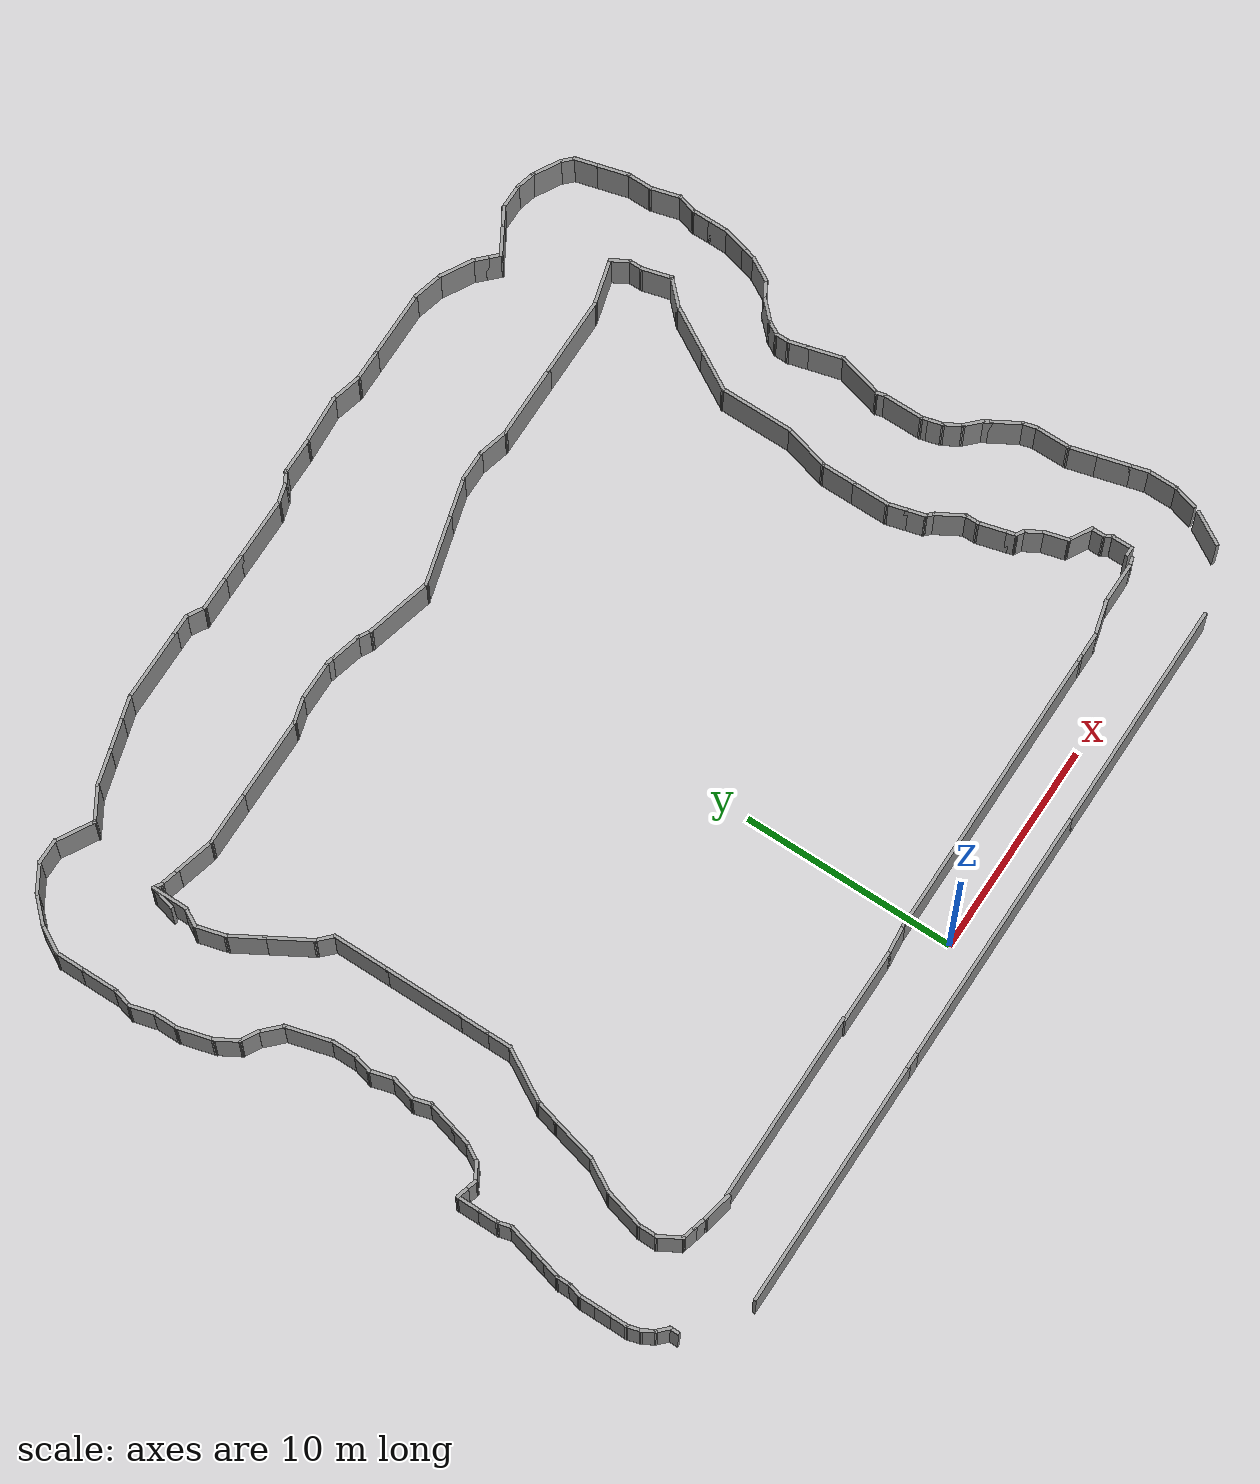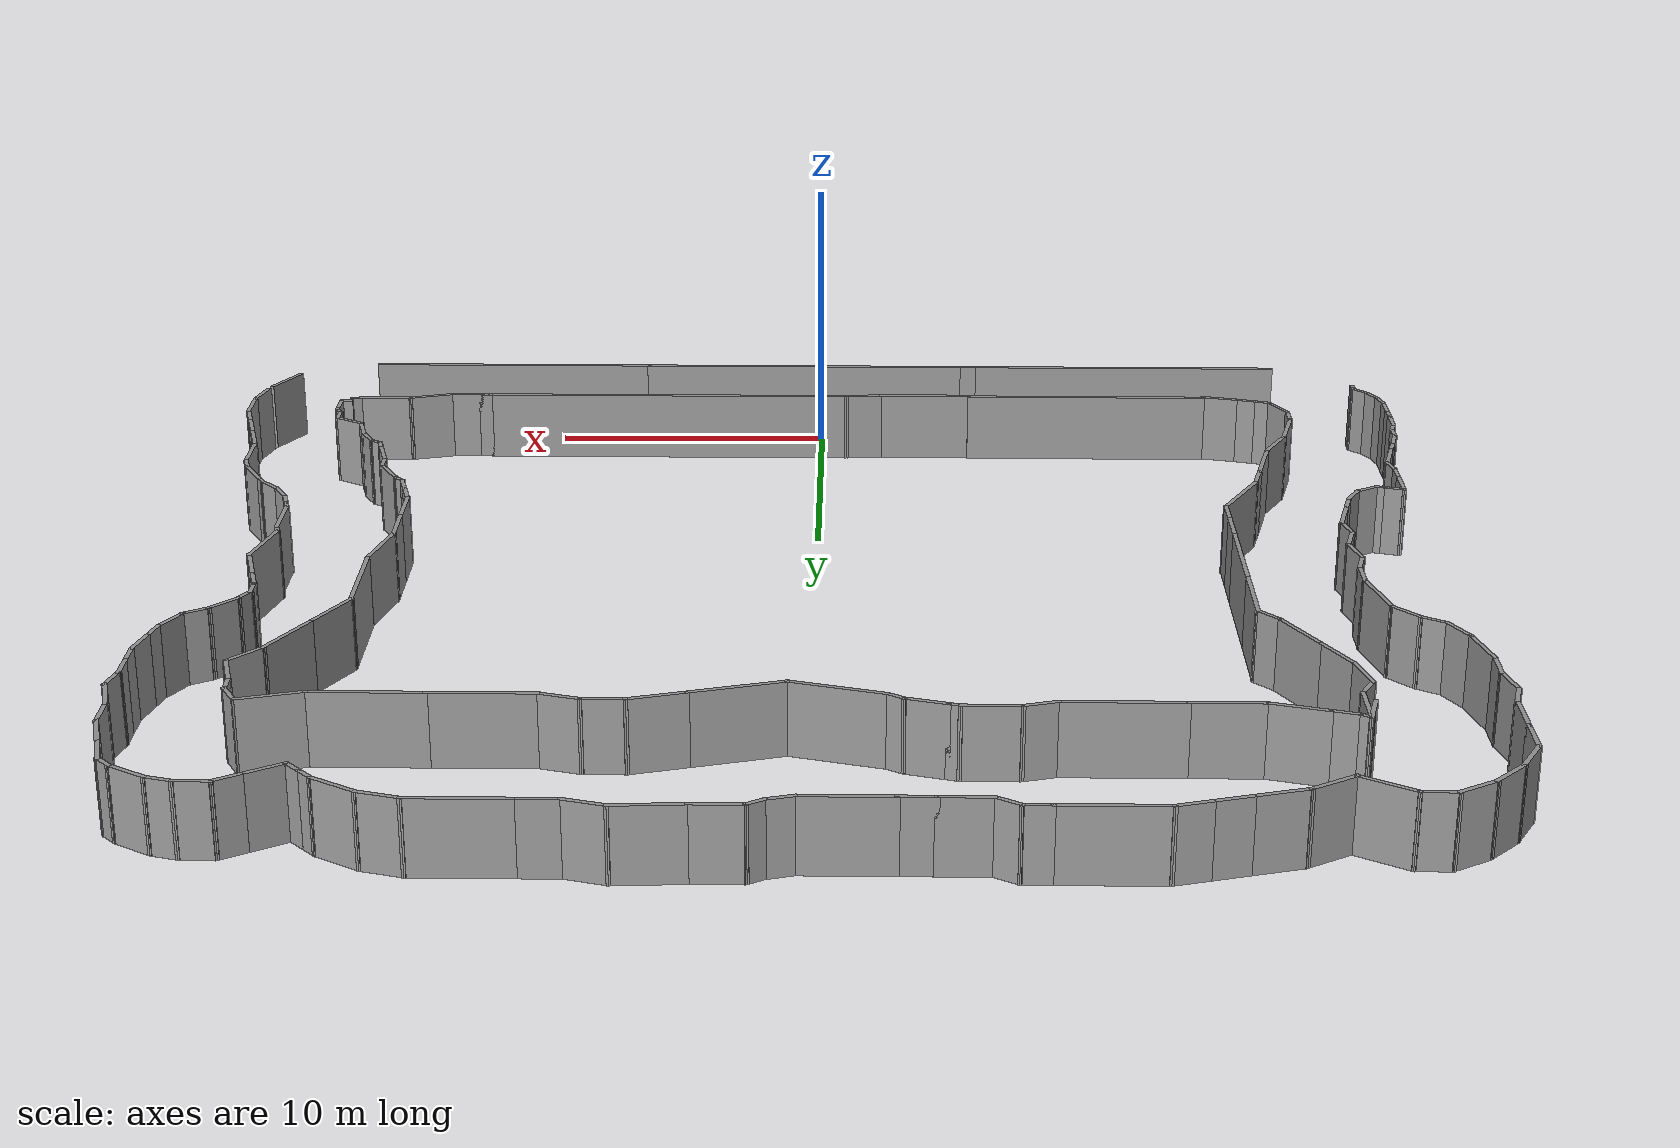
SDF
<sdf version="1.7">
 <world name="default">
  <light name="sun" type="directional">
   <pose>0 0 10 0 -0 0</pose>
   <diffuse>0.8 0.8 0.8 1</diffuse>
   <specular>0.2 0.2 0.2 1</specular>
   <attenuation>
    <range>1000</range>
    <constant>0.9</constant>
    <linear>0.01</linear>
    <quadratic>0.001</quadratic>
   </attenuation>
   <direction>-0.5 0.1 -0.9</direction>
   <spot><inner_angle>0</inner_angle><outer_angle>0</outer_angle><falloff>0</falloff></spot>
  </light>
  <scene>
   <grid>0</grid>
   <shadows>0</shadows>
   <ambient>0.4 0.4 0.4 1</ambient>
   <background>0.7 0.7 0.7 1</background>
  </scene>
  <gravity>0 0 -9.8</gravity>
  <magnetic_field>6e-06 2.3e-05 -4.2e-05</magnetic_field>
  <atmosphere type="adiabatic"/>
  <physics type="ode">
   <max_step_size>0.001</max_step_size>
   <real_time_factor>1</real_time_factor>
   <real_time_update_rate>1000</real_time_update_rate>
  </physics>
  <audio><device>default</device></audio>
  <spherical_coordinates>
   <surface_model>EARTH_WGS84</surface_model>
   <latitude_deg>0</latitude_deg>
   <longitude_deg>0</longitude_deg>
   <elevation>0</elevation>
   <heading_deg>0</heading_deg>
  </spherical_coordinates>
  <model name="Untitled">
   <pose>0.112024 16.4674 0 0 -0 0</pose>
   <link name="Wall_10">
    <collision name="Wall_10_Collision">
     <geometry><box><size>3.50824 0.15 2.5</size></box></geometry>
     <pose>0 0 1.25 0 -0 0</pose>
    </collision>
    <visual name="Wall_10_Visual">
     <pose>0 0 1.25 0 -0 0</pose>
     <geometry><box><size>3.50824 0.15 2.5</size></box></geometry>
     <material>
      <script><uri>file://media/materials/scripts/gazebo.material</uri><name>Gazebo/Grey</name></script>
      <ambient>1 1 1 1</ambient>
     </material>
     <meta><layer>0</layer></meta>
    </visual>
    <pose>-4.08498 -14.7597 0 0 -0 0</pose>
   </link>
   <link name="Wall_100">
    <collision name="Wall_100_Collision">
     <geometry><box><size>1.5 0.15 2.5</size></box></geometry>
     <pose>0 0 1.25 0 -0 0</pose>
    </collision>
    <visual name="Wall_100_Visual">
     <pose>0 0 1.25 0 -0 0</pose>
     <geometry><box><size>1.5 0.15 2.5</size></box></geometry>
     <material>
      <script><uri>file://media/materials/scripts/gazebo.material</uri><name>Gazebo/Grey</name></script>
      <ambient>1 1 1 1</ambient>
     </material>
     <meta><layer>0</layer></meta>
    </visual>
    <pose>19.9845 -6.51025 0 0 -0 2.0944</pose>
   </link>
   <link name="Wall_101">
    <collision name="Wall_101_Collision">
     <geometry><box><size>0.5 0.15 2.5</size></box></geometry>
     <pose>0 0 1.25 0 -0 0</pose>
    </collision>
    <visual name="Wall_101_Visual">
     <pose>0 0 1.25 0 -0 0</pose>
     <geometry><box><size>0.5 0.15 2.5</size></box></geometry>
     <material>
      <script><uri>file://media/materials/scripts/gazebo.material</uri><name>Gazebo/Grey</name></script>
      <ambient>1 1 1 1</ambient>
     </material>
     <meta><layer>0</layer></meta>
    </visual>
    <pose>19.5595 -5.77413 0 0 -0 2.0944</pose>
   </link>
   <link name="Wall_102">
    <collision name="Wall_102_Collision">
     <geometry><box><size>1 0.15 2.5</size></box></geometry>
     <pose>0 0 1.25 0 -0 0</pose>
    </collision>
    <visual name="Wall_102_Visual">
     <pose>0 0 1.25 0 -0 0</pose>
     <geometry><box><size>1 0.15 2.5</size></box></geometry>
     <material>
      <script><uri>file://media/materials/scripts/gazebo.material</uri><name>Gazebo/Grey</name></script>
      <ambient>1 1 1 1</ambient>
     </material>
     <meta><layer>0</layer></meta>
    </visual>
    <pose>19.1715 -5.32205 0 0 -0 2.35619</pose>
   </link>
   <link name="Wall_103">
    <collision name="Wall_103_Collision">
     <geometry><box><size>1 0.15 2.5</size></box></geometry>
     <pose>0 0 1.25 0 -0 0</pose>
    </collision>
    <visual name="Wall_103_Visual">
     <pose>0 0 1.25 0 -0 0</pose>
     <geometry><box><size>1 0.15 2.5</size></box></geometry>
     <material>
      <script><uri>file://media/materials/scripts/gazebo.material</uri><name>Gazebo/Grey</name></script>
      <ambient>1 1 1 1</ambient>
     </material>
     <meta><layer>0</layer></meta>
    </visual>
    <pose>18.6585 -4.65347 0 0 -0 2.0944</pose>
   </link>
   <link name="Wall_104">
    <collision name="Wall_104_Collision">
     <geometry><box><size>0.75 0.15 2.5</size></box></geometry>
     <pose>0 0 1.25 0 -0 0</pose>
    </collision>
    <visual name="Wall_104_Visual">
     <pose>0 0 1.25 0 -0 0</pose>
     <geometry><box><size>0.75 0.15 2.5</size></box></geometry>
     <material>
      <script><uri>file://media/materials/scripts/gazebo.material</uri><name>Gazebo/Grey</name></script>
      <ambient>1 1 1 1</ambient>
     </material>
     <meta><layer>0</layer></meta>
    </visual>
    <pose>18.3683 -3.99564 0 0 -0 1.8326</pose>
   </link>
   <link name="Wall_105">
    <collision name="Wall_105_Collision">
     <geometry><box><size>0.5 0.15 2.5</size></box></geometry>
     <pose>0 0 1.25 0 -0 0</pose>
    </collision>
    <visual name="Wall_105_Visual">
     <pose>0 0 1.25 0 -0 0</pose>
     <geometry><box><size>0.5 0.15 2.5</size></box></geometry>
     <material>
      <script><uri>file://media/materials/scripts/gazebo.material</uri><name>Gazebo/Grey</name></script>
      <ambient>1 1 1 1</ambient>
     </material>
     <meta><layer>0</layer></meta>
    </visual>
    <pose>18.2454 -3.53682 0 0 -0 1.8326</pose>
   </link>
   <link name="Wall_106">
    <collision name="Wall_106_Collision">
     <geometry><box><size>2 0.15 2.5</size></box></geometry>
     <pose>0 0 1.25 0 -0 0</pose>
    </collision>
    <visual name="Wall_106_Visual">
     <pose>0 0 1.25 0 -0 0</pose>
     <geometry><box><size>2 0.15 2.5</size></box></geometry>
     <material>
      <script><uri>file://media/materials/scripts/gazebo.material</uri><name>Gazebo/Grey</name></script>
      <ambient>1 1 1 1</ambient>
     </material>
     <meta><layer>0</layer></meta>
    </visual>
    <pose>18.2001 -2.44278 0 0 -0 1.5708</pose>
   </link>
   <link name="Wall_107">
    <collision name="Wall_107_Collision">
     <geometry><box><size>0.5 0.15 2.5</size></box></geometry>
     <pose>0 0 1.25 0 -0 0</pose>
    </collision>
    <visual name="Wall_107_Visual">
     <pose>0 0 1.25 0 -0 0</pose>
     <geometry><box><size>0.5 0.15 2.5</size></box></geometry>
     <material>
      <script><uri>file://media/materials/scripts/gazebo.material</uri><name>Gazebo/Grey</name></script>
      <ambient>1 1 1 1</ambient>
     </material>
     <meta><layer>0</layer></meta>
    </visual>
    <pose>18.1548 -1.34875 0 0 -0 1.8326</pose>
   </link>
   <link name="Wall_108">
    <collision name="Wall_108_Collision">
     <geometry><box><size>2.25 0.15 2.5</size></box></geometry>
     <pose>0 0 1.25 0 -0 0</pose>
    </collision>
    <visual name="Wall_108_Visual">
     <pose>0 0 1.25 0 -0 0</pose>
     <geometry><box><size>2.25 0.15 2.5</size></box></geometry>
     <material>
      <script><uri>file://media/materials/scripts/gazebo.material</uri><name>Gazebo/Grey</name></script>
      <ambient>1 1 1 1</ambient>
     </material>
     <meta><layer>0</layer></meta>
    </visual>
    <pose>18.3813 -0.165486 0 0 -0 1.309</pose>
   </link>
   <link name="Wall_109">
    <collision name="Wall_109_Collision">
     <geometry><box><size>1.75 0.15 2.5</size></box></geometry>
     <pose>0 0 1.25 0 -0 0</pose>
    </collision>
    <visual name="Wall_109_Visual">
     <pose>0 0 1.25 0 -0 0</pose>
     <geometry><box><size>1.75 0.15 2.5</size></box></geometry>
     <material>
      <script><uri>file://media/materials/scripts/gazebo.material</uri><name>Gazebo/Grey</name></script>
      <ambient>1 1 1 1</ambient>
     </material>
     <meta><layer>0</layer></meta>
    </visual>
    <pose>18.446 1.62148 0 0 -0 1.8326</pose>
   </link>
   <link name="Wall_110">
    <collision name="Wall_110_Collision">
     <geometry><box><size>1 0.15 2.5</size></box></geometry>
     <pose>0 0 1.25 0 -0 0</pose>
    </collision>
    <visual name="Wall_110_Visual">
     <pose>0 0 1.25 0 -0 0</pose>
     <geometry><box><size>1 0.15 2.5</size></box></geometry>
     <material>
      <script><uri>file://media/materials/scripts/gazebo.material</uri><name>Gazebo/Grey</name></script>
      <ambient>1 1 1 1</ambient>
     </material>
     <meta><layer>0</layer></meta>
    </visual>
    <pose>18.1289 2.80473 0 0 -0 1.8326</pose>
   </link>
   <link name="Wall_111">
    <collision name="Wall_111_Collision">
     <geometry><box><size>0.75 0.15 2.5</size></box></geometry>
     <pose>0 0 1.25 0 -0 0</pose>
    </collision>
    <visual name="Wall_111_Visual">
     <pose>0 0 1.25 0 -0 0</pose>
     <geometry><box><size>0.75 0.15 2.5</size></box></geometry>
     <material>
      <script><uri>file://media/materials/scripts/gazebo.material</uri><name>Gazebo/Grey</name></script>
      <ambient>1 1 1 1</ambient>
     </material>
     <meta><layer>0</layer></meta>
    </visual>
    <pose>18.0189 3.51525 0 0 -0 1.5708</pose>
   </link>
   <link name="Wall_112">
    <collision name="Wall_112_Collision">
     <geometry><box><size>0.75 0.15 2.5</size></box></geometry>
     <pose>0 0 1.25 0 -0 0</pose>
    </collision>
    <visual name="Wall_112_Visual">
     <pose>0 0 1.25 0 -0 0</pose>
     <geometry><box><size>0.75 0.15 2.5</size></box></geometry>
     <material>
      <script><uri>file://media/materials/scripts/gazebo.material</uri><name>Gazebo/Grey</name></script>
      <ambient>1 1 1 1</ambient>
     </material>
     <meta><layer>0</layer></meta>
    </visual>
    <pose>18.1689 4.07506 0 0 -0 1.0472</pose>
   </link>
   <link name="Wall_113">
    <collision name="Wall_113_Collision">
     <geometry><box><size>1.25 0.15 2.5</size></box></geometry>
     <pose>0 0 1.25 0 -0 0</pose>
    </collision>
    <visual name="Wall_113_Visual">
     <pose>0 0 1.25 0 -0 0</pose>
     <geometry><box><size>1.25 0.15 2.5</size></box></geometry>
     <material>
      <script><uri>file://media/materials/scripts/gazebo.material</uri><name>Gazebo/Grey</name></script>
      <ambient>1 1 1 1</ambient>
     </material>
     <meta><layer>0</layer></meta>
    </visual>
    <pose>18.7078 4.72378 0 0 -0 0.785398</pose>
   </link>
   <link name="Wall_114">
    <collision name="Wall_114_Collision">
     <geometry><box><size>1 0.15 2.5</size></box></geometry>
     <pose>0 0 1.25 0 -0 0</pose>
    </collision>
    <visual name="Wall_114_Visual">
     <pose>0 0 1.25 0 -0 0</pose>
     <geometry><box><size>1 0.15 2.5</size></box></geometry>
     <material>
      <script><uri>file://media/materials/scripts/gazebo.material</uri><name>Gazebo/Grey</name></script>
      <ambient>1 1 1 1</ambient>
     </material>
     <meta><layer>0</layer></meta>
    </visual>
    <pose>19.4648 5.32519 0 0 -0 0.523599</pose>
   </link>
   <link name="Wall_115">
    <collision name="Wall_115_Collision">
     <geometry><box><size>1.25 0.15 2.5</size></box></geometry>
     <pose>0 0 1.25 0 -0 0</pose>
    </collision>
    <visual name="Wall_115_Visual">
     <pose>0 0 1.25 0 -0 0</pose>
     <geometry><box><size>1.25 0.15 2.5</size></box></geometry>
     <material>
      <script><uri>file://media/materials/scripts/gazebo.material</uri><name>Gazebo/Grey</name></script>
      <ambient>1 1 1 1</ambient>
     </material>
     <meta><layer>0</layer></meta>
    </visual>
    <pose>20.1078 6.014 0 0 -0 1.0472</pose>
   </link>
   <link name="Wall_116">
    <collision name="Wall_116_Collision">
     <geometry><box><size>0.75 0.15 2.5</size></box></geometry>
     <pose>0 0 1.25 0 -0 0</pose>
    </collision>
    <visual name="Wall_116_Visual">
     <pose>0 0 1.25 0 -0 0</pose>
     <geometry><box><size>0.75 0.15 2.5</size></box></geometry>
     <material>
      <script><uri>file://media/materials/scripts/gazebo.material</uri><name>Gazebo/Grey</name></script>
      <ambient>1 1 1 1</ambient>
     </material>
     <meta><layer>0</layer></meta>
    </visual>
    <pose>20.4605 6.78009 0 0 -0 1.309</pose>
   </link>
   <link name="Wall_117">
    <collision name="Wall_117_Collision">
     <geometry><box><size>1.25 0.15 2.5</size></box></geometry>
     <pose>0 0 1.25 0 -0 0</pose>
    </collision>
    <visual name="Wall_117_Visual">
     <pose>0 0 1.25 0 -0 0</pose>
     <geometry><box><size>1.25 0.15 2.5</size></box></geometry>
     <material>
      <script><uri>file://media/materials/scripts/gazebo.material</uri><name>Gazebo/Grey</name></script>
      <ambient>1 1 1 1</ambient>
     </material>
     <meta><layer>0</layer></meta>
    </visual>
    <pose>20.6805 7.60113 0 0 -0 1.309</pose>
   </link>
   <link name="Wall_118">
    <collision name="Wall_118_Collision">
     <geometry><box><size>1 0.15 2.5</size></box></geometry>
     <pose>0 0 1.25 0 -0 0</pose>
    </collision>
    <visual name="Wall_118_Visual">
     <pose>0 0 1.25 0 -0 0</pose>
     <geometry><box><size>1 0.15 2.5</size></box></geometry>
     <material>
      <script><uri>file://media/materials/scripts/gazebo.material</uri><name>Gazebo/Grey</name></script>
      <ambient>1 1 1 1</ambient>
     </material>
     <meta><layer>0</layer></meta>
    </visual>
    <pose>20.8228 8.55739 0 0 -0 1.5708</pose>
   </link>
   <link name="Wall_119">
    <collision name="Wall_119_Collision">
     <geometry><box><size>1 0.15 2.5</size></box></geometry>
     <pose>0 0 1.25 0 -0 0</pose>
    </collision>
    <visual name="Wall_119_Visual">
     <pose>0 0 1.25 0 -0 0</pose>
     <geometry><box><size>1 0.15 2.5</size></box></geometry>
     <material>
      <script><uri>file://media/materials/scripts/gazebo.material</uri><name>Gazebo/Grey</name></script>
      <ambient>1 1 1 1</ambient>
     </material>
     <meta><layer>0</layer></meta>
    </visual>
    <pose>20.8228 9.40739 0 0 -0 1.5708</pose>
   </link>
   <link name="Wall_12">
    <collision name="Wall_12_Collision">
     <geometry><box><size>1.49108 0.15 2.5</size></box></geometry>
     <pose>0 0 1.25 0 -0 0</pose>
    </collision>
    <visual name="Wall_12_Visual">
     <pose>0 0 1.25 0 -0 0</pose>
     <geometry><box><size>1.49108 0.15 2.5</size></box></geometry>
     <material>
      <script><uri>file://media/materials/scripts/gazebo.material</uri><name>Gazebo/Grey</name></script>
      <ambient>1 1 1 1</ambient>
     </material>
     <meta><layer>0</layer></meta>
    </visual>
    <pose>-1.73855 -14.699 0 0 -0 -3.05097</pose>
   </link>
   <link name="Wall_120">
    <collision name="Wall_120_Collision">
     <geometry><box><size>1 0.15 2.5</size></box></geometry>
     <pose>0 0 1.25 0 -0 0</pose>
    </collision>
    <visual name="Wall_120_Visual">
     <pose>0 0 1.25 0 -0 0</pose>
     <geometry><box><size>1 0.15 2.5</size></box></geometry>
     <material>
      <script><uri>file://media/materials/scripts/gazebo.material</uri><name>Gazebo/Grey</name></script>
      <ambient>1 1 1 1</ambient>
     </material>
     <meta><layer>0</layer></meta>
    </visual>
    <pose>20.9328 10.2429 0 0 -0 1.309</pose>
   </link>
   <link name="Wall_121">
    <collision name="Wall_121_Collision">
     <geometry><box><size>1.5 0.15 2.5</size></box></geometry>
     <pose>0 0 1.25 0 -0 0</pose>
    </collision>
    <visual name="Wall_121_Visual">
     <pose>0 0 1.25 0 -0 0</pose>
     <geometry><box><size>1.5 0.15 2.5</size></box></geometry>
     <material>
      <script><uri>file://media/materials/scripts/gazebo.material</uri><name>Gazebo/Grey</name></script>
      <ambient>1 1 1 1</ambient>
     </material>
     <meta><layer>0</layer></meta>
    </visual>
    <pose>20.8681 11.3054 0 0 -0 1.8326</pose>
   </link>
   <link name="Wall_122">
    <collision name="Wall_122_Collision">
     <geometry><box><size>1.25 0.15 2.5</size></box></geometry>
     <pose>0 0 1.25 0 -0 0</pose>
    </collision>
    <visual name="Wall_122_Visual">
     <pose>0 0 1.25 0 -0 0</pose>
     <geometry><box><size>1.25 0.15 2.5</size></box></geometry>
     <material>
      <script><uri>file://media/materials/scripts/gazebo.material</uri><name>Gazebo/Grey</name></script>
      <ambient>1 1 1 1</ambient>
     </material>
     <meta><layer>0</layer></meta>
    </visual>
    <pose>20.6934 12.5074 0 0 -0 1.5708</pose>
   </link>
   <link name="Wall_123">
    <collision name="Wall_123_Collision">
     <geometry><box><size>1.5 0.15 2.5</size></box></geometry>
     <pose>0 0 1.25 0 -0 0</pose>
    </collision>
    <visual name="Wall_123_Visual">
     <pose>0 0 1.25 0 -0 0</pose>
     <geometry><box><size>1.5 0.15 2.5</size></box></geometry>
     <material>
      <script><uri>file://media/materials/scripts/gazebo.material</uri><name>Gazebo/Grey</name></script>
      <ambient>1 1 1 1</ambient>
     </material>
     <meta><layer>0</layer></meta>
    </visual>
    <pose>20.5187 13.7094 0 0 -0 1.8326</pose>
   </link>
   <link name="Wall_124">
    <collision name="Wall_124_Collision">
     <geometry><box><size>1.25 0.15 2.5</size></box></geometry>
     <pose>0 0 1.25 0 -0 0</pose>
    </collision>
    <visual name="Wall_124_Visual">
     <pose>0 0 1.25 0 -0 0</pose>
     <geometry><box><size>1.25 0.15 2.5</size></box></geometry>
     <material>
      <script><uri>file://media/materials/scripts/gazebo.material</uri><name>Gazebo/Grey</name></script>
      <ambient>1 1 1 1</ambient>
     </material>
     <meta><layer>0</layer></meta>
    </visual>
    <pose>20.2017 14.8927 0 0 -0 1.8326</pose>
   </link>
   <link name="Wall_125">
    <collision name="Wall_125_Collision">
     <geometry><box><size>0.75 0.15 2.5</size></box></geometry>
     <pose>0 0 1.25 0 -0 0</pose>
    </collision>
    <visual name="Wall_125_Visual">
     <pose>0 0 1.25 0 -0 0</pose>
     <geometry><box><size>0.75 0.15 2.5</size></box></geometry>
     <material>
      <script><uri>file://media/materials/scripts/gazebo.material</uri><name>Gazebo/Grey</name></script>
      <ambient>1 1 1 1</ambient>
     </material>
     <meta><layer>0</layer></meta>
    </visual>
    <pose>19.8472 15.6361 0 0 -0 2.35619</pose>
   </link>
   <link name="Wall_126">
    <collision name="Wall_126_Collision">
     <geometry><box><size>1.5 0.15 2.5</size></box></geometry>
     <pose>0 0 1.25 0 -0 0</pose>
    </collision>
    <visual name="Wall_126_Visual">
     <pose>0 0 1.25 0 -0 0</pose>
     <geometry><box><size>1.5 0.15 2.5</size></box></geometry>
     <material>
      <script><uri>file://media/materials/scripts/gazebo.material</uri><name>Gazebo/Grey</name></script>
      <ambient>1 1 1 1</ambient>
     </material>
     <meta><layer>0</layer></meta>
    </visual>
    <pose>19.0505 16.1857 0 0 -0 2.61799</pose>
   </link>
   <link name="Wall_127">
    <collision name="Wall_127_Collision">
     <geometry><box><size>1 0.15 2.5</size></box></geometry>
     <pose>0 0 1.25 0 -0 0</pose>
    </collision>
    <visual name="Wall_127_Visual">
     <pose>0 0 1.25 0 -0 0</pose>
     <geometry><box><size>1 0.15 2.5</size></box></geometry>
     <material>
      <script><uri>file://media/materials/scripts/gazebo.material</uri><name>Gazebo/Grey</name></script>
      <ambient>1 1 1 1</ambient>
     </material>
     <meta><layer>0</layer></meta>
    </visual>
    <pose>18.0554 16.6332 0 0 -0 2.87979</pose>
   </link>
   <link name="Wall_128">
    <collision name="Wall_128_Collision">
     <geometry><box><size>1.25 0.15 2.5</size></box></geometry>
     <pose>0 0 1.25 0 -0 0</pose>
    </collision>
    <visual name="Wall_128_Visual">
     <pose>0 0 1.25 0 -0 0</pose>
     <geometry><box><size>1.25 0.15 2.5</size></box></geometry>
     <material>
      <script><uri>file://media/materials/scripts/gazebo.material</uri><name>Gazebo/Grey</name></script>
      <ambient>1 1 1 1</ambient>
     </material>
     <meta><layer>0</layer></meta>
    </visual>
    <pose>17.0949 16.7432 0 0 -0 3.14159</pose>
   </link>
   <link name="Wall_129">
    <collision name="Wall_129_Collision">
     <geometry><box><size>1 0.15 2.5</size></box></geometry>
     <pose>0 0 1.25 0 -0 0</pose>
    </collision>
    <visual name="Wall_129_Visual">
     <pose>0 0 1.25 0 -0 0</pose>
     <geometry><box><size>1 0.15 2.5</size></box></geometry>
     <material>
      <script><uri>file://media/materials/scripts/gazebo.material</uri><name>Gazebo/Grey</name></script>
      <ambient>1 1 1 1</ambient>
     </material>
     <meta><layer>0</layer></meta>
    </visual>
    <pose>16.1768 16.5307 0 0 -0 -2.61799</pose>
   </link>
   <link name="Wall_130">
    <collision name="Wall_130_Collision">
     <geometry><box><size>1.5 0.15 2.5</size></box></geometry>
     <pose>0 0 1.25 0 -0 0</pose>
    </collision>
    <visual name="Wall_130_Visual">
     <pose>0 0 1.25 0 -0 0</pose>
     <geometry><box><size>1.5 0.15 2.5</size></box></geometry>
     <material>
      <script><uri>file://media/materials/scripts/gazebo.material</uri><name>Gazebo/Grey</name></script>
      <ambient>1 1 1 1</ambient>
     </material>
     <meta><layer>0</layer></meta>
    </visual>
    <pose>15.2242 15.9807 0 0 -0 -2.61799</pose>
   </link>
   <link name="Wall_131">
    <collision name="Wall_131_Collision">
     <geometry><box><size>0.75 0.15 2.5</size></box></geometry>
     <pose>0 0 1.25 0 -0 0</pose>
    </collision>
    <visual name="Wall_131_Visual">
     <pose>0 0 1.25 0 -0 0</pose>
     <geometry><box><size>0.75 0.15 2.5</size></box></geometry>
     <material>
      <script><uri>file://media/materials/scripts/gazebo.material</uri><name>Gazebo/Grey</name></script>
      <ambient>1 1 1 1</ambient>
     </material>
     <meta><layer>0</layer></meta>
    </visual>
    <pose>14.4275 15.8553 0 0 -0 2.35619</pose>
   </link>
   <link name="Wall_132">
    <collision name="Wall_132_Collision">
     <geometry><box><size>0.75 0.15 2.5</size></box></geometry>
     <pose>0 0 1.25 0 -0 0</pose>
    </collision>
    <visual name="Wall_132_Visual">
     <pose>0 0 1.25 0 -0 0</pose>
     <geometry><box><size>0.75 0.15 2.5</size></box></geometry>
     <material>
      <script><uri>file://media/materials/scripts/gazebo.material</uri><name>Gazebo/Grey</name></script>
      <ambient>1 1 1 1</ambient>
     </material>
     <meta><layer>0</layer></meta>
    </visual>
    <pose>14.0032 16.2796 0 0 -0 2.35619</pose>
   </link>
   <link name="Wall_133">
    <collision name="Wall_133_Collision">
     <geometry><box><size>1.75 0.15 2.5</size></box></geometry>
     <pose>0 0 1.25 0 -0 0</pose>
    </collision>
    <visual name="Wall_133_Visual">
     <pose>0 0 1.25 0 -0 0</pose>
     <geometry><box><size>1.75 0.15 2.5</size></box></geometry>
     <material>
      <script><uri>file://media/materials/scripts/gazebo.material</uri><name>Gazebo/Grey</name></script>
      <ambient>1 1 1 1</ambient>
     </material>
     <meta><layer>0</layer></meta>
    </visual>
    <pose>13.0983 16.8917 0 0 -0 2.61799</pose>
   </link>
   <link name="Wall_134">
    <collision name="Wall_134_Collision">
     <geometry><box><size>1.5 0.15 2.5</size></box></geometry>
     <pose>0 0 1.25 0 -0 0</pose>
    </collision>
    <visual name="Wall_134_Visual">
     <pose>0 0 1.25 0 -0 0</pose>
     <geometry><box><size>1.5 0.15 2.5</size></box></geometry>
     <material>
      <script><uri>file://media/materials/scripts/gazebo.material</uri><name>Gazebo/Grey</name></script>
      <ambient>1 1 1 1</ambient>
     </material>
     <meta><layer>0</layer></meta>
    </visual>
    <pose>11.7535 17.4664 0 0 -0 2.87979</pose>
   </link>
   <link name="Wall_135">
    <collision name="Wall_135_Collision">
     <geometry><box><size>3.25 0.15 2.5</size></box></geometry>
     <pose>0 0 1.25 0 -0 0</pose>
    </collision>
    <visual name="Wall_135_Visual">
     <pose>0 0 1.25 0 -0 0</pose>
     <geometry><box><size>3.25 0.15 2.5</size></box></geometry>
     <material>
      <script><uri>file://media/materials/scripts/gazebo.material</uri><name>Gazebo/Grey</name></script>
      <ambient>1 1 1 1</ambient>
     </material>
     <meta><layer>0</layer></meta>
    </visual>
    <pose>9.55146 17.6411 0 0 -0 3.14159</pose>
   </link>
   <link name="Wall_136">
    <collision name="Wall_136_Collision">
     <geometry><box><size>1.5 0.15 2.5</size></box></geometry>
     <pose>0 0 1.25 0 -0 0</pose>
    </collision>
    <visual name="Wall_136_Visual">
     <pose>0 0 1.25 0 -0 0</pose>
     <geometry><box><size>1.5 0.15 2.5</size></box></geometry>
     <material>
      <script><uri>file://media/materials/scripts/gazebo.material</uri><name>Gazebo/Grey</name></script>
      <ambient>1 1 1 1</ambient>
     </material>
     <meta><layer>0</layer></meta>
    </visual>
    <pose>7.32646 17.6411 0 0 -0 3.14159</pose>
   </link>
   <link name="Wall_137">
    <collision name="Wall_137_Collision">
     <geometry><box><size>1.5 0.15 2.5</size></box></geometry>
     <pose>0 0 1.25 0 -0 0</pose>
    </collision>
    <visual name="Wall_137_Visual">
     <pose>0 0 1.25 0 -0 0</pose>
     <geometry><box><size>1.5 0.15 2.5</size></box></geometry>
     <material>
      <script><uri>file://media/materials/scripts/gazebo.material</uri><name>Gazebo/Grey</name></script>
      <ambient>1 1 1 1</ambient>
     </material>
     <meta><layer>0</layer></meta>
    </visual>
    <pose>5.99946 17.8158 0 0 -0 2.87979</pose>
   </link>
   <link name="Wall_14">
    <collision name="Wall_14_Collision">
     <geometry><box><size>13.75 0.15 2.5</size></box></geometry>
     <pose>0 0 1.25 0 -0 0</pose>
    </collision>
    <visual name="Wall_14_Visual">
     <pose>0 0 1.25 0 -0 0</pose>
     <geometry><box><size>13.75 0.15 2.5</size></box></geometry>
     <material>
      <script><uri>file://media/materials/scripts/gazebo.material</uri><name>Gazebo/Grey</name></script>
      <ambient>1 1 1 1</ambient>
     </material>
     <meta><layer>0</layer></meta>
    </visual>
    <pose>5.72924 -14.6384 0 0 -0 0</pose>
   </link>
   <link name="Wall_141">
    <collision name="Wall_141_Collision">
     <geometry><box><size>0.5 0.15 2.5</size></box></geometry>
     <pose>0 0 1.25 0 -0 0</pose>
    </collision>
    <visual name="Wall_141_Visual">
     <pose>0 0 1.25 0 -0 0</pose>
     <geometry><box><size>0.5 0.15 2.5</size></box></geometry>
     <material>
      <script><uri>file://media/materials/scripts/gazebo.material</uri><name>Gazebo/Grey</name></script>
      <ambient>1 1 1 1</ambient>
     </material>
     <meta><layer>0</layer></meta>
    </visual>
    <pose>-20.5165 -15.9262 0 0 -0 -1.5708</pose>
   </link>
   <link name="Wall_143">
    <collision name="Wall_143_Collision">
     <geometry><box><size>0.75 0.15 2.5</size></box></geometry>
     <pose>0 0 1.25 0 -0 0</pose>
    </collision>
    <visual name="Wall_143_Visual">
     <pose>0 0 1.25 0 -0 0</pose>
     <geometry><box><size>0.75 0.15 2.5</size></box></geometry>
     <material>
      <script><uri>file://media/materials/scripts/gazebo.material</uri><name>Gazebo/Grey</name></script>
      <ambient>1 1 1 1</ambient>
     </material>
     <meta><layer>0</layer></meta>
    </visual>
    <pose>-20.7287 -15.539 0 0 -0 2.35619</pose>
   </link>
   <link name="Wall_144">
    <collision name="Wall_144_Collision">
     <geometry><box><size>0.75 0.15 2.5</size></box></geometry>
     <pose>0 0 1.25 0 -0 0</pose>
    </collision>
    <visual name="Wall_144_Visual">
     <pose>0 0 1.25 0 -0 0</pose>
     <geometry><box><size>0.75 0.15 2.5</size></box></geometry>
     <material>
      <script><uri>file://media/materials/scripts/gazebo.material</uri><name>Gazebo/Grey</name></script>
      <ambient>1 1 1 1</ambient>
     </material>
     <meta><layer>0</layer></meta>
    </visual>
    <pose>-21.0908 -15.0671 0 0 -0 2.0944</pose>
   </link>
   <link name="Wall_145">
    <collision name="Wall_145_Collision">
     <geometry><box><size>0.75 0.15 2.5</size></box></geometry>
     <pose>0 0 1.25 0 -0 0</pose>
    </collision>
    <visual name="Wall_145_Visual">
     <pose>0 0 1.25 0 -0 0</pose>
     <geometry><box><size>0.75 0.15 2.5</size></box></geometry>
     <material>
      <script><uri>file://media/materials/scripts/gazebo.material</uri><name>Gazebo/Grey</name></script>
      <ambient>1 1 1 1</ambient>
     </material>
     <meta><layer>0</layer></meta>
    </visual>
    <pose>-21.3185 -14.5175 0 0 -0 1.8326</pose>
   </link>
   <link name="Wall_146">
    <collision name="Wall_146_Collision">
     <geometry><box><size>1 0.15 2.5</size></box></geometry>
     <pose>0 0 1.25 0 -0 0</pose>
    </collision>
    <visual name="Wall_146_Visual">
     <pose>0 0 1.25 0 -0 0</pose>
     <geometry><box><size>1 0.15 2.5</size></box></geometry>
     <material>
      <script><uri>file://media/materials/scripts/gazebo.material</uri><name>Gazebo/Grey</name></script>
      <ambient>1 1 1 1</ambient>
     </material>
     <meta><layer>0</layer></meta>
    </visual>
    <pose>-21.3961 -13.8027 0 0 -0 1.5708</pose>
   </link>
   <link name="Wall_147">
    <collision name="Wall_147_Collision">
     <geometry><box><size>0.75 0.15 2.5</size></box></geometry>
     <pose>0 0 1.25 0 -0 0</pose>
    </collision>
    <visual name="Wall_147_Visual">
     <pose>0 0 1.25 0 -0 0</pose>
     <geometry><box><size>0.75 0.15 2.5</size></box></geometry>
     <material>
      <script><uri>file://media/materials/scripts/gazebo.material</uri><name>Gazebo/Grey</name></script>
      <ambient>1 1 1 1</ambient>
     </material>
     <meta><layer>0</layer></meta>
    </visual>
    <pose>-21.3961 -13.0777 0 0 -0 1.5708</pose>
   </link>
   <link name="Wall_148">
    <collision name="Wall_148_Collision">
     <geometry><box><size>1 0.15 2.5</size></box></geometry>
     <pose>0 0 1.25 0 -0 0</pose>
    </collision>
    <visual name="Wall_148_Visual">
     <pose>0 0 1.25 0 -0 0</pose>
     <geometry><box><size>1 0.15 2.5</size></box></geometry>
     <material>
      <script><uri>file://media/materials/scripts/gazebo.material</uri><name>Gazebo/Grey</name></script>
      <ambient>1 1 1 1</ambient>
     </material>
     <meta><layer>0</layer></meta>
    </visual>
    <pose>-21.3961 -12.3527 0 0 -0 1.5708</pose>
   </link>
   <link name="Wall_149">
    <collision name="Wall_149_Collision">
     <geometry><box><size>0.75 0.15 2.5</size></box></geometry>
     <pose>0 0 1.25 0 -0 0</pose>
    </collision>
    <visual name="Wall_149_Visual">
     <pose>0 0 1.25 0 -0 0</pose>
     <geometry><box><size>0.75 0.15 2.5</size></box></geometry>
     <material>
      <script><uri>file://media/materials/scripts/gazebo.material</uri><name>Gazebo/Grey</name></script>
      <ambient>1 1 1 1</ambient>
     </material>
     <meta><layer>0</layer></meta>
    </visual>
    <pose>-21.3185 -11.638 0 0 -0 1.309</pose>
   </link>
   <link name="Wall_15">
    <collision name="Wall_15_Collision">
     <geometry><box><size>0.5 0.15 2.5</size></box></geometry>
     <pose>0 0 1.25 0 -0 0</pose>
    </collision>
    <visual name="Wall_15_Visual">
     <pose>0 0 1.25 0 -0 0</pose>
     <geometry><box><size>0.5 0.15 2.5</size></box></geometry>
     <material>
      <script><uri>file://media/materials/scripts/gazebo.material</uri><name>Gazebo/Grey</name></script>
      <ambient>1 1 1 1</ambient>
     </material>
     <meta><layer>0</layer></meta>
    </visual>
    <pose>12.7042 -14.6384 0 0 -0 0</pose>
   </link>
   <link name="Wall_150">
    <collision name="Wall_150_Collision">
     <geometry><box><size>0.75 0.15 2.5</size></box></geometry>
     <pose>0 0 1.25 0 -0 0</pose>
    </collision>
    <visual name="Wall_150_Visual">
     <pose>0 0 1.25 0 -0 0</pose>
     <geometry><box><size>0.75 0.15 2.5</size></box></geometry>
     <material>
      <script><uri>file://media/materials/scripts/gazebo.material</uri><name>Gazebo/Grey</name></script>
      <ambient>1 1 1 1</ambient>
     </material>
     <meta><layer>0</layer></meta>
    </visual>
    <pose>-21.2408 -11.0482 0 0 -0 1.5708</pose>
   </link>
   <link name="Wall_151">
    <collision name="Wall_151_Collision">
     <geometry><box><size>1 0.15 2.5</size></box></geometry>
     <pose>0 0 1.25 0 -0 0</pose>
    </collision>
    <visual name="Wall_151_Visual">
     <pose>0 0 1.25 0 -0 0</pose>
     <geometry><box><size>1 0.15 2.5</size></box></geometry>
     <material>
      <script><uri>file://media/materials/scripts/gazebo.material</uri><name>Gazebo/Grey</name></script>
      <ambient>1 1 1 1</ambient>
     </material>
     <meta><layer>0</layer></meta>
    </visual>
    <pose>-21.1308 -10.3377 0 0 -0 1.309</pose>
   </link>
   <link name="Wall_152">
    <collision name="Wall_152_Collision">
     <geometry><box><size>0.75 0.15 2.5</size></box></geometry>
     <pose>0 0 1.25 0 -0 0</pose>
    </collision>
    <visual name="Wall_152_Visual">
     <pose>0 0 1.25 0 -0 0</pose>
     <geometry><box><size>0.75 0.15 2.5</size></box></geometry>
     <material>
      <script><uri>file://media/materials/scripts/gazebo.material</uri><name>Gazebo/Grey</name></script>
      <ambient>1 1 1 1</ambient>
     </material>
     <meta><layer>0</layer></meta>
    </visual>
    <pose>-20.9432 -9.63737 0 0 -0 1.309</pose>
   </link>
   <link name="Wall_153">
    <collision name="Wall_153_Collision">
     <geometry><box><size>1.5 0.15 2.5</size></box></geometry>
     <pose>0 0 1.25 0 -0 0</pose>
    </collision>
    <visual name="Wall_153_Visual">
     <pose>0 0 1.25 0 -0 0</pose>
     <geometry><box><size>1.5 0.15 2.5</size></box></geometry>
     <material>
      <script><uri>file://media/materials/scripts/gazebo.material</uri><name>Gazebo/Grey</name></script>
      <ambient>1 1 1 1</ambient>
     </material>
     <meta><layer>0</layer></meta>
    </visual>
    <pose>-20.6908 -8.69559 0 0 -0 1.309</pose>
   </link>
   <link name="Wall_154">
    <collision name="Wall_154_Collision">
     <geometry><box><size>0.75 0.15 2.5</size></box></geometry>
     <pose>0 0 1.25 0 -0 0</pose>
    </collision>
    <visual name="Wall_154_Visual">
     <pose>0 0 1.25 0 -0 0</pose>
     <geometry><box><size>0.75 0.15 2.5</size></box></geometry>
     <material>
      <script><uri>file://media/materials/scripts/gazebo.material</uri><name>Gazebo/Grey</name></script>
      <ambient>1 1 1 1</ambient>
     </material>
     <meta><layer>0</layer></meta>
    </visual>
    <pose>-20.5938 -7.75381 0 0 -0 1.8326</pose>
   </link>
   <link name="Wall_155">
    <collision name="Wall_155_Collision">
     <geometry><box><size>1 0.15 2.5</size></box></geometry>
     <pose>0 0 1.25 0 -0 0</pose>
    </collision>
    <visual name="Wall_155_Visual">
     <pose>0 0 1.25 0 -0 0</pose>
     <geometry><box><size>1 0.15 2.5</size></box></geometry>
     <material>
      <script><uri>file://media/materials/scripts/gazebo.material</uri><name>Gazebo/Grey</name></script>
      <ambient>1 1 1 1</ambient>
     </material>
     <meta><layer>0</layer></meta>
    </visual>
    <pose>-20.6714 -7.03904 0 0 -0 1.5708</pose>
   </link>
   <link name="Wall_156">
    <collision name="Wall_156_Collision">
     <geometry><box><size>1.25 0.15 2.5</size></box></geometry>
     <pose>0 0 1.25 0 -0 0</pose>
    </collision>
    <visual name="Wall_156_Visual">
     <pose>0 0 1.25 0 -0 0</pose>
     <geometry><box><size>1.25 0.15 2.5</size></box></geometry>
     <material>
      <script><uri>file://media/materials/scripts/gazebo.material</uri><name>Gazebo/Grey</name></script>
      <ambient>1 1 1 1</ambient>
     </material>
     <meta><layer>0</layer></meta>
    </visual>
    <pose>-20.6714 -6.06403 0 0 -0 1.5708</pose>
   </link>
   <link name="Wall_157">
    <collision name="Wall_157_Collision">
     <geometry><box><size>0.75 0.15 2.5</size></box></geometry>
     <pose>0 0 1.25 0 -0 0</pose>
    </collision>
    <visual name="Wall_157_Visual">
     <pose>0 0 1.25 0 -0 0</pose>
     <geometry><box><size>0.75 0.15 2.5</size></box></geometry>
     <material>
      <script><uri>file://media/materials/scripts/gazebo.material</uri><name>Gazebo/Grey</name></script>
      <ambient>1 1 1 1</ambient>
     </material>
     <meta><layer>0</layer></meta>
    </visual>
    <pose>-20.3816 -5.59168 0 0 -0 -0.261799</pose>
   </link>
   <link name="Wall_158">
    <collision name="Wall_158_Collision">
     <geometry><box><size>0.5 0.15 2.5</size></box></geometry>
     <pose>0 0 1.25 0 -0 0</pose>
    </collision>
    <visual name="Wall_158_Visual">
     <pose>0 0 1.25 0 -0 0</pose>
     <geometry><box><size>0.5 0.15 2.5</size></box></geometry>
     <material>
      <script><uri>file://media/materials/scripts/gazebo.material</uri><name>Gazebo/Grey</name></script>
      <ambient>1 1 1 1</ambient>
     </material>
     <meta><layer>0</layer></meta>
    </visual>
    <pose>-19.9228 -5.71462 0 0 -0 -0.261799</pose>
   </link>
   <link name="Wall_159">
    <collision name="Wall_159_Collision">
     <geometry><box><size>1 0.15 2.5</size></box></geometry>
     <pose>0 0 1.25 0 -0 0</pose>
    </collision>
    <visual name="Wall_159_Visual">
     <pose>0 0 1.25 0 -0 0</pose>
     <geometry><box><size>1 0.15 2.5</size></box></geometry>
     <material>
      <script><uri>file://media/materials/scripts/gazebo.material</uri><name>Gazebo/Grey</name></script>
      <ambient>1 1 1 1</ambient>
     </material>
     <meta><layer>0</layer></meta>
    </visual>
    <pose>-19.3857 -5.54741 0 0 -0 0.523599</pose>
   </link>
   <link name="Wall_16">
    <collision name="Wall_16_Collision">
     <geometry><box><size>1.25 0.15 2.5</size></box></geometry>
     <pose>0 0 1.25 0 -0 0</pose>
    </collision>
    <visual name="Wall_16_Visual">
     <pose>0 0 1.25 0 -0 0</pose>
     <geometry><box><size>1.25 0.15 2.5</size></box></geometry>
     <material>
      <script><uri>file://media/materials/scripts/gazebo.material</uri><name>Gazebo/Grey</name></script>
      <ambient>1 1 1 1</ambient>
     </material>
     <meta><layer>0</layer></meta>
    </visual>
    <pose>13.4292 -14.6384 0 0 -0 0</pose>
   </link>
   <link name="Wall_160">
    <collision name="Wall_160_Collision">
     <geometry><box><size>1 0.15 2.5</size></box></geometry>
     <pose>0 0 1.25 0 -0 0</pose>
    </collision>
    <visual name="Wall_160_Visual">
     <pose>0 0 1.25 0 -0 0</pose>
     <geometry><box><size>1 0.15 2.5</size></box></geometry>
     <material>
      <script><uri>file://media/materials/scripts/gazebo.material</uri><name>Gazebo/Grey</name></script>
      <ambient>1 1 1 1</ambient>
     </material>
     <meta><layer>0</layer></meta>
    </visual>
    <pose>-18.8052 -4.96685 0 0 -0 1.0472</pose>
   </link>
   <link name="Wall_161">
    <collision name="Wall_161_Collision">
     <geometry><box><size>1 0.15 2.5</size></box></geometry>
     <pose>0 0 1.25 0 -0 0</pose>
    </collision>
    <visual name="Wall_161_Visual">
     <pose>0 0 1.25 0 -0 0</pose>
     <geometry><box><size>1 0.15 2.5</size></box></geometry>
     <material>
      <script><uri>file://media/materials/scripts/gazebo.material</uri><name>Gazebo/Grey</name></script>
      <ambient>1 1 1 1</ambient>
     </material>
     <meta><layer>0</layer></meta>
    </visual>
    <pose>-18.4827 -4.18827 0 0 -0 1.309</pose>
   </link>
   <link name="Wall_162">
    <collision name="Wall_162_Collision">
     <geometry><box><size>1.5 0.15 2.5</size></box></geometry>
     <pose>0 0 1.25 0 -0 0</pose>
    </collision>
    <visual name="Wall_162_Visual">
     <pose>0 0 1.25 0 -0 0</pose>
     <geometry><box><size>1.5 0.15 2.5</size></box></geometry>
     <material>
      <script><uri>file://media/materials/scripts/gazebo.material</uri><name>Gazebo/Grey</name></script>
      <ambient>1 1 1 1</ambient>
     </material>
     <meta><layer>0</layer></meta>
    </visual>
    <pose>-18.198 -3.12575 0 0 -0 1.309</pose>
   </link>
   <link name="Wall_163">
    <collision name="Wall_163_Collision">
     <geometry><box><size>1 0.15 2.5</size></box></geometry>
     <pose>0 0 1.25 0 -0 0</pose>
    </collision>
    <visual name="Wall_163_Visual">
     <pose>0 0 1.25 0 -0 0</pose>
     <geometry><box><size>1 0.15 2.5</size></box></geometry>
     <material>
      <script><uri>file://media/materials/scripts/gazebo.material</uri><name>Gazebo/Grey</name></script>
      <ambient>1 1 1 1</ambient>
     </material>
     <meta><layer>0</layer></meta>
    </visual>
    <pose>-18.1332 -2.06324 0 0 -0 1.8326</pose>
   </link>
   <link name="Wall_164">
    <collision name="Wall_164_Collision">
     <geometry><box><size>1.25 0.15 2.5</size></box></geometry>
     <pose>0 0 1.25 0 -0 0</pose>
    </collision>
    <visual name="Wall_164_Visual">
     <pose>0 0 1.25 0 -0 0</pose>
     <geometry><box><size>1.25 0.15 2.5</size></box></geometry>
     <material>
      <script><uri>file://media/materials/scripts/gazebo.material</uri><name>Gazebo/Grey</name></script>
      <ambient>1 1 1 1</ambient>
     </material>
     <meta><layer>0</layer></meta>
    </visual>
    <pose>-18.1009 -1.12146 0 0 -0 1.309</pose>
   </link>
   <link name="Wall_165">
    <collision name="Wall_165_Collision">
     <geometry><box><size>1.25 0.15 2.5</size></box></geometry>
     <pose>0 0 1.25 0 -0 0</pose>
    </collision>
    <visual name="Wall_165_Visual">
     <pose>0 0 1.25 0 -0 0</pose>
     <geometry><box><size>1.25 0.15 2.5</size></box></geometry>
     <material>
      <script><uri>file://media/materials/scripts/gazebo.material</uri><name>Gazebo/Grey</name></script>
      <ambient>1 1 1 1</ambient>
     </material>
     <meta><layer>0</layer></meta>
    </visual>
    <pose>-18.1009 -0.05894 0 0 -0 1.8326</pose>
   </link>
   <link name="Wall_166">
    <collision name="Wall_166_Collision">
     <geometry><box><size>1 0.15 2.5</size></box></geometry>
     <pose>0 0 1.25 0 -0 0</pose>
    </collision>
    <visual name="Wall_166_Visual">
     <pose>0 0 1.25 0 -0 0</pose>
     <geometry><box><size>1 0.15 2.5</size></box></geometry>
     <material>
      <script><uri>file://media/materials/scripts/gazebo.material</uri><name>Gazebo/Grey</name></script>
      <ambient>1 1 1 1</ambient>
     </material>
     <meta><layer>0</layer></meta>
    </visual>
    <pose>-18.1332 0.882838 0 0 -0 1.309</pose>
   </link>
   <link name="Wall_167">
    <collision name="Wall_167_Collision">
     <geometry><box><size>1.25 0.15 2.5</size></box></geometry>
     <pose>0 0 1.25 0 -0 0</pose>
    </collision>
    <visual name="Wall_167_Visual">
     <pose>0 0 1.25 0 -0 0</pose>
     <geometry><box><size>1.25 0.15 2.5</size></box></geometry>
     <material>
      <script><uri>file://media/materials/scripts/gazebo.material</uri><name>Gazebo/Grey</name></script>
      <ambient>1 1 1 1</ambient>
     </material>
     <meta><layer>0</layer></meta>
    </visual>
    <pose>-18.0233 1.84336 0 0 -0 1.5708</pose>
   </link>
   <link name="Wall_168">
    <collision name="Wall_168_Collision">
     <geometry><box><size>2.25 0.15 2.5</size></box></geometry>
     <pose>0 0 1.25 0 -0 0</pose>
    </collision>
    <visual name="Wall_168_Visual">
     <pose>0 0 1.25 0 -0 0</pose>
     <geometry><box><size>2.25 0.15 2.5</size></box></geometry>
     <material>
      <script><uri>file://media/materials/scripts/gazebo.material</uri><name>Gazebo/Grey</name></script>
      <ambient>1 1 1 1</ambient>
     </material>
     <meta><layer>0</layer></meta>
    </visual>
    <pose>-18.295 3.40758 0 0 -0 1.8326</pose>
   </link>
   <link name="Wall_169">
    <collision name="Wall_169_Collision">
     <geometry><box><size>1.25 0.15 2.5</size></box></geometry>
     <pose>0 0 1.25 0 -0 0</pose>
    </collision>
    <visual name="Wall_169_Visual">
     <pose>0 0 1.25 0 -0 0</pose>
     <geometry><box><size>1.25 0.15 2.5</size></box></geometry>
     <material>
      <script><uri>file://media/materials/scripts/gazebo.material</uri><name>Gazebo/Grey</name></script>
      <ambient>1 1 1 1</ambient>
     </material>
     <meta><layer>0</layer></meta>
    </visual>
    <pose>-18.9557 4.81071 0 0 -0 2.35619</pose>
   </link>
   <link name="Wall_17">
    <collision name="Wall_17_Collision">
     <geometry><box><size>1.75 0.15 2.5</size></box></geometry>
     <pose>0 0 1.25 0 -0 0</pose>
    </collision>
    <visual name="Wall_17_Visual">
     <pose>0 0 1.25 0 -0 0</pose>
     <geometry><box><size>1.75 0.15 2.5</size></box></geometry>
     <material>
      <script><uri>file://media/materials/scripts/gazebo.material</uri><name>Gazebo/Grey</name></script>
      <ambient>1 1 1 1</ambient>
     </material>
     <meta><layer>0</layer></meta>
    </visual>
    <pose>14.752 -14.4313 0 0 -0 0.261799</pose>
   </link>
   <link name="Wall_170">
    <collision name="Wall_170_Collision">
     <geometry><box><size>1 0.15 2.5</size></box></geometry>
     <pose>0 0 1.25 0 -0 0</pose>
    </collision>
    <visual name="Wall_170_Visual">
     <pose>0 0 1.25 0 -0 0</pose>
     <geometry><box><size>1 0.15 2.5</size></box></geometry>
     <material>
      <script><uri>file://media/materials/scripts/gazebo.material</uri><name>Gazebo/Grey</name></script>
      <ambient>1 1 1 1</ambient>
     </material>
     <meta><layer>0</layer></meta>
    </visual>
    <pose>-19.7126 5.41212 0 0 -0 2.61799</pose>
   </link>
   <link name="Wall_171">
    <collision name="Wall_171_Collision">
     <geometry><box><size>1.25 0.15 2.5</size></box></geometry>
     <pose>0 0 1.25 0 -0 0</pose>
    </collision>
    <visual name="Wall_171_Visual">
     <pose>0 0 1.25 0 -0 0</pose>
     <geometry><box><size>1.25 0.15 2.5</size></box></geometry>
     <material>
      <script><uri>file://media/materials/scripts/gazebo.material</uri><name>Gazebo/Grey</name></script>
      <ambient>1 1 1 1</ambient>
     </material>
     <meta><layer>0</layer></meta>
    </visual>
    <pose>-20.3557 6.10093 0 0 -0 2.0944</pose>
   </link>
   <link name="Wall_172">
    <collision name="Wall_172_Collision">
     <geometry><box><size>1.75 0.15 2.5</size></box></geometry>
     <pose>0 0 1.25 0 -0 0</pose>
    </collision>
    <visual name="Wall_172_Visual">
     <pose>0 0 1.25 0 -0 0</pose>
     <geometry><box><size>1.75 0.15 2.5</size></box></geometry>
     <material>
      <script><uri>file://media/materials/scripts/gazebo.material</uri><name>Gazebo/Grey</name></script>
      <ambient>1 1 1 1</ambient>
     </material>
     <meta><layer>0</layer></meta>
    </visual>
    <pose>-20.8378 7.34999 0 0 -0 1.8326</pose>
   </link>
   <link name="Wall_173">
    <collision name="Wall_173_Collision">
     <geometry><box><size>1.25 0.15 2.5</size></box></geometry>
     <pose>0 0 1.25 0 -0 0</pose>
    </collision>
    <visual name="Wall_173_Visual">
     <pose>0 0 1.25 0 -0 0</pose>
     <geometry><box><size>1.25 0.15 2.5</size></box></geometry>
     <material>
      <script><uri>file://media/materials/scripts/gazebo.material</uri><name>Gazebo/Grey</name></script>
      <ambient>1 1 1 1</ambient>
     </material>
     <meta><layer>0</layer></meta>
    </visual>
    <pose>-21.0448 8.67273 0 0 -0 1.5708</pose>
   </link>
   <link name="Wall_174">
    <collision name="Wall_174_Collision">
     <geometry><box><size>1.25 0.15 2.5</size></box></geometry>
     <pose>0 0 1.25 0 -0 0</pose>
    </collision>
    <visual name="Wall_174_Visual">
     <pose>0 0 1.25 0 -0 0</pose>
     <geometry><box><size>1.25 0.15 2.5</size></box></geometry>
     <material>
      <script><uri>file://media/materials/scripts/gazebo.material</uri><name>Gazebo/Grey</name></script>
      <ambient>1 1 1 1</ambient>
     </material>
     <meta><layer>0</layer></meta>
    </visual>
    <pose>-21.1872 9.75399 0 0 -0 1.8326</pose>
   </link>
   <link name="Wall_175">
    <collision name="Wall_175_Collision">
     <geometry><box><size>1 0.15 2.5</size></box></geometry>
     <pose>0 0 1.25 0 -0 0</pose>
    </collision>
    <visual name="Wall_175_Visual">
     <pose>0 0 1.25 0 -0 0</pose>
     <geometry><box><size>1 0.15 2.5</size></box></geometry>
     <material>
      <script><uri>file://media/materials/scripts/gazebo.material</uri><name>Gazebo/Grey</name></script>
      <ambient>1 1 1 1</ambient>
     </material>
     <meta><layer>0</layer></meta>
    </visual>
    <pose>-21.2195 10.6958 0 0 -0 1.309</pose>
   </link>
   <link name="Wall_176">
    <collision name="Wall_176_Collision">
     <geometry><box><size>1.75 0.15 2.5</size></box></geometry>
     <pose>0 0 1.25 0 -0 0</pose>
    </collision>
    <visual name="Wall_176_Visual">
     <pose>0 0 1.25 0 -0 0</pose>
     <geometry><box><size>1.75 0.15 2.5</size></box></geometry>
     <material>
      <script><uri>file://media/materials/scripts/gazebo.material</uri><name>Gazebo/Grey</name></script>
      <ambient>1 1 1 1</ambient>
     </material>
     <meta><layer>0</layer></meta>
    </visual>
    <pose>-21.1095 11.9063 0 0 -0 1.5708</pose>
   </link>
   <link name="Wall_177">
    <collision name="Wall_177_Collision">
     <geometry><box><size>1.5 0.15 2.5</size></box></geometry>
     <pose>0 0 1.25 0 -0 0</pose>
    </collision>
    <visual name="Wall_177_Visual">
     <pose>0 0 1.25 0 -0 0</pose>
     <geometry><box><size>1.5 0.15 2.5</size></box></geometry>
     <material>
      <script><uri>file://media/materials/scripts/gazebo.material</uri><name>Gazebo/Grey</name></script>
      <ambient>1 1 1 1</ambient>
     </material>
     <meta><layer>0</layer></meta>
    </visual>
    <pose>-21.1095 13.3813 0 0 -0 1.5708</pose>
   </link>
   <link name="Wall_178">
    <collision name="Wall_178_Collision">
     <geometry><box><size>1.5 0.15 2.5</size></box></geometry>
     <pose>0 0 1.25 0 -0 0</pose>
    </collision>
    <visual name="Wall_178_Visual">
     <pose>0 0 1.25 0 -0 0</pose>
     <geometry><box><size>1.5 0.15 2.5</size></box></geometry>
     <material>
      <script><uri>file://media/materials/scripts/gazebo.material</uri><name>Gazebo/Grey</name></script>
      <ambient>1 1 1 1</ambient>
     </material>
     <meta><layer>0</layer></meta>
    </visual>
    <pose>-20.772 14.6408 0 0 -0 1.0472</pose>
   </link>
   <link name="Wall_179">
    <collision name="Wall_179_Collision">
     <geometry><box><size>1.5 0.15 2.5</size></box></geometry>
     <pose>0 0 1.25 0 -0 0</pose>
    </collision>
    <visual name="Wall_179_Visual">
     <pose>0 0 1.25 0 -0 0</pose>
     <geometry><box><size>1.5 0.15 2.5</size></box></geometry>
     <material>
      <script><uri>file://media/materials/scripts/gazebo.material</uri><name>Gazebo/Grey</name></script>
      <ambient>1 1 1 1</ambient>
     </material>
     <meta><layer>0</layer></meta>
    </visual>
    <pose>-19.9572 15.7027 0 0 -0 0.785398</pose>
   </link>
   <link name="Wall_18">
    <collision name="Wall_18_Collision">
     <geometry><box><size>2 0.15 2.5</size></box></geometry>
     <pose>0 0 1.25 0 -0 0</pose>
    </collision>
    <visual name="Wall_18_Visual">
     <pose>0 0 1.25 0 -0 0</pose>
     <geometry><box><size>2 0.15 2.5</size></box></geometry>
     <material>
      <script><uri>file://media/materials/scripts/gazebo.material</uri><name>Gazebo/Grey</name></script>
      <ambient>1 1 1 1</ambient>
     </material>
     <meta><layer>0</layer></meta>
    </visual>
    <pose>16.4497 -14.2243 0 0 -0 0</pose>
   </link>
   <link name="Wall_180">
    <collision name="Wall_180_Collision">
     <geometry><box><size>1.5 0.15 2.5</size></box></geometry>
     <pose>0 0 1.25 0 -0 0</pose>
    </collision>
    <visual name="Wall_180_Visual">
     <pose>0 0 1.25 0 -0 0</pose>
     <geometry><box><size>1.5 0.15 2.5</size></box></geometry>
     <material>
      <script><uri>file://media/materials/scripts/gazebo.material</uri><name>Gazebo/Grey</name></script>
      <ambient>1 1 1 1</ambient>
     </material>
     <meta><layer>0</layer></meta>
    </visual>
    <pose>-18.8954 16.5175 0 0 -0 0.523599</pose>
   </link>
   <link name="Wall_181">
    <collision name="Wall_181_Collision">
     <geometry><box><size>1.25 0.15 2.5</size></box></geometry>
     <pose>0 0 1.25 0 -0 0</pose>
    </collision>
    <visual name="Wall_181_Visual">
     <pose>0 0 1.25 0 -0 0</pose>
     <geometry><box><size>1.25 0.15 2.5</size></box></geometry>
     <material>
      <script><uri>file://media/materials/scripts/gazebo.material</uri><name>Gazebo/Grey</name></script>
      <ambient>1 1 1 1</ambient>
     </material>
     <meta><layer>0</layer></meta>
    </visual>
    <pose>-17.7608 16.855 0 0 -0 0</pose>
   </link>
   <link name="Wall_182">
    <collision name="Wall_182_Collision">
     <geometry><box><size>2 0.15 2.5</size></box></geometry>
     <pose>0 0 1.25 0 -0 0</pose>
    </collision>
    <visual name="Wall_182_Visual">
     <pose>0 0 1.25 0 -0 0</pose>
     <geometry><box><size>2 0.15 2.5</size></box></geometry>
     <material>
      <script><uri>file://media/materials/scripts/gazebo.material</uri><name>Gazebo/Grey</name></script>
      <ambient>1 1 1 1</ambient>
     </material>
     <meta><layer>0</layer></meta>
    </visual>
    <pose>-16.4097 16.3925 0 0 -0 -0.523599</pose>
   </link>
   <link name="Wall_183">
    <collision name="Wall_183_Collision">
     <geometry><box><size>1.75 0.15 2.5</size></box></geometry>
     <pose>0 0 1.25 0 -0 0</pose>
    </collision>
    <visual name="Wall_183_Visual">
     <pose>0 0 1.25 0 -0 0</pose>
     <geometry><box><size>1.75 0.15 2.5</size></box></geometry>
     <material>
      <script><uri>file://media/materials/scripts/gazebo.material</uri><name>Gazebo/Grey</name></script>
      <ambient>1 1 1 1</ambient>
     </material>
     <meta><layer>0</layer></meta>
    </visual>
    <pose>-14.9158 16.33 0 0 -0 0.523599</pose>
   </link>
   <link name="Wall_184">
    <collision name="Wall_184_Collision">
     <geometry><box><size>1.75 0.15 2.5</size></box></geometry>
     <pose>0 0 1.25 0 -0 0</pose>
    </collision>
    <visual name="Wall_184_Visual">
     <pose>0 0 1.25 0 -0 0</pose>
     <geometry><box><size>1.75 0.15 2.5</size></box></geometry>
     <material>
      <script><uri>file://media/materials/scripts/gazebo.material</uri><name>Gazebo/Grey</name></script>
      <ambient>1 1 1 1</ambient>
     </material>
     <meta><layer>0</layer></meta>
    </visual>
    <pose>-13.4503 16.9371 0 0 -0 0.261799</pose>
   </link>
   <link name="Wall_185">
    <collision name="Wall_185_Collision">
     <geometry><box><size>1.5 0.15 2.5</size></box></geometry>
     <pose>0 0 1.25 0 -0 0</pose>
    </collision>
    <visual name="Wall_185_Visual">
     <pose>0 0 1.25 0 -0 0</pose>
     <geometry><box><size>1.5 0.15 2.5</size></box></geometry>
     <material>
      <script><uri>file://media/materials/scripts/gazebo.material</uri><name>Gazebo/Grey</name></script>
      <ambient>1 1 1 1</ambient>
     </material>
     <meta><layer>0</layer></meta>
    </visual>
    <pose>-12.0255 17.3188 0 0 -0 0.261799</pose>
   </link>
   <link name="Wall_186">
    <collision name="Wall_186_Collision">
     <geometry><box><size>1.25 0.15 2.5</size></box></geometry>
     <pose>0 0 1.25 0 -0 0</pose>
    </collision>
    <visual name="Wall_186_Visual">
     <pose>0 0 1.25 0 -0 0</pose>
     <geometry><box><size>1.25 0.15 2.5</size></box></geometry>
     <material>
      <script><uri>file://media/materials/scripts/gazebo.material</uri><name>Gazebo/Grey</name></script>
      <ambient>1 1 1 1</ambient>
     </material>
     <meta><layer>0</layer></meta>
    </visual>
    <pose>-10.8423 17.6359 0 0 -0 0.261799</pose>
   </link>
   <link name="Wall_187">
    <collision name="Wall_187_Collision">
     <geometry><box><size>3.5 0.15 2.5</size></box></geometry>
     <pose>0 0 1.25 0 -0 0</pose>
    </collision>
    <visual name="Wall_187_Visual">
     <pose>0 0 1.25 0 -0 0</pose>
     <geometry><box><size>3.5 0.15 2.5</size></box></geometry>
     <material>
      <script><uri>file://media/materials/scripts/gazebo.material</uri><name>Gazebo/Grey</name></script>
      <ambient>1 1 1 1</ambient>
     </material>
     <meta><layer>0</layer></meta>
    </visual>
    <pose>-8.63601 17.7782 0 0 -0 0</pose>
   </link>
   <link name="Wall_188">
    <collision name="Wall_188_Collision">
     <geometry><box><size>1 0.15 2.5</size></box></geometry>
     <pose>0 0 1.25 0 -0 0</pose>
    </collision>
    <visual name="Wall_188_Visual">
     <pose>0 0 1.25 0 -0 0</pose>
     <geometry><box><size>1 0.15 2.5</size></box></geometry>
     <material>
      <script><uri>file://media/materials/scripts/gazebo.material</uri><name>Gazebo/Grey</name></script>
      <ambient>1 1 1 1</ambient>
     </material>
     <meta><layer>0</layer></meta>
    </visual>
    <pose>-6.53601 17.7782 0 0 -0 0</pose>
   </link>
   <link name="Wall_189">
    <collision name="Wall_189_Collision">
     <geometry><box><size>1 0.15 2.5</size></box></geometry>
     <pose>0 0 1.25 0 -0 0</pose>
    </collision>
    <visual name="Wall_189_Visual">
     <pose>0 0 1.25 0 -0 0</pose>
     <geometry><box><size>1 0.15 2.5</size></box></geometry>
     <material>
      <script><uri>file://media/materials/scripts/gazebo.material</uri><name>Gazebo/Grey</name></script>
      <ambient>1 1 1 1</ambient>
     </material>
     <meta><layer>0</layer></meta>
    </visual>
    <pose>-5.74295 17.5657 0 0 -0 -0.523599</pose>
   </link>
   <link name="Wall_19">
    <collision name="Wall_19_Collision">
     <geometry><box><size>0.5 0.15 2.5</size></box></geometry>
     <pose>0 0 1.25 0 -0 0</pose>
    </collision>
    <visual name="Wall_19_Visual">
     <pose>0 0 1.25 0 -0 0</pose>
     <geometry><box><size>0.5 0.15 2.5</size></box></geometry>
     <material>
      <script><uri>file://media/materials/scripts/gazebo.material</uri><name>Gazebo/Grey</name></script>
      <ambient>1 1 1 1</ambient>
     </material>
     <meta><layer>0</layer></meta>
    </visual>
    <pose>17.5438 -14.179 0 0 -0 0.261799</pose>
   </link>
   <link name="Wall_190">
    <collision name="Wall_190_Collision">
     <geometry><box><size>1.75 0.15 2.5</size></box></geometry>
     <pose>0 0 1.25 0 -0 0</pose>
    </collision>
    <visual name="Wall_190_Visual">
     <pose>0 0 1.25 0 -0 0</pose>
     <geometry><box><size>1.75 0.15 2.5</size></box></geometry>
     <material>
      <script><uri>file://media/materials/scripts/gazebo.material</uri><name>Gazebo/Grey</name></script>
      <ambient>1 1 1 1</ambient>
     </material>
     <meta><layer>0</layer></meta>
    </visual>
    <pose>-4.57489 17.3532 0 0 -0 0</pose>
   </link>
   <link name="Wall_191">
    <collision name="Wall_191_Collision">
     <geometry><box><size>1.25 0.15 2.5</size></box></geometry>
     <pose>0 0 1.25 0 -0 0</pose>
    </collision>
    <visual name="Wall_191_Visual">
     <pose>0 0 1.25 0 -0 0</pose>
     <geometry><box><size>1.25 0.15 2.5</size></box></geometry>
     <material>
      <script><uri>file://media/materials/scripts/gazebo.material</uri><name>Gazebo/Grey</name></script>
      <ambient>1 1 1 1</ambient>
     </material>
     <meta><layer>0</layer></meta>
    </visual>
    <pose>-3.22489 17.3532 0 0 -0 0</pose>
   </link>
   <link name="Wall_192">
    <collision name="Wall_192_Collision">
     <geometry><box><size>3 0.15 2.5</size></box></geometry>
     <pose>0 0 1.25 0 -0 0</pose>
    </collision>
    <visual name="Wall_192_Visual">
     <pose>0 0 1.25 0 -0 0</pose>
     <geometry><box><size>3 0.15 2.5</size></box></geometry>
     <material>
      <script><uri>file://media/materials/scripts/gazebo.material</uri><name>Gazebo/Grey</name></script>
      <ambient>1 1 1 1</ambient>
     </material>
     <meta><layer>0</layer></meta>
    </visual>
    <pose>-1.24989 17.3532 0 0 -0 0</pose>
   </link>
   <link name="Wall_193">
    <collision name="Wall_193_Collision">
     <geometry><box><size>1 0.15 2.5</size></box></geometry>
     <pose>0 0 1.25 0 -0 0</pose>
    </collision>
    <visual name="Wall_193_Visual">
     <pose>0 0 1.25 0 -0 0</pose>
     <geometry><box><size>1 0.15 2.5</size></box></geometry>
     <material>
      <script><uri>file://media/materials/scripts/gazebo.material</uri><name>Gazebo/Grey</name></script>
      <ambient>1 1 1 1</ambient>
     </material>
     <meta><layer>0</layer></meta>
    </visual>
    <pose>0.585631 17.4632 0 0 -0 0.261799</pose>
   </link>
   <link name="Wall_194">
    <collision name="Wall_194_Collision">
     <geometry><box><size>0.75 0.15 2.5</size></box></geometry>
     <pose>0 0 1.25 0 -0 0</pose>
    </collision>
    <visual name="Wall_194_Visual">
     <pose>0 0 1.25 0 -0 0</pose>
     <geometry><box><size>0.75 0.15 2.5</size></box></geometry>
     <material>
      <script><uri>file://media/materials/scripts/gazebo.material</uri><name>Gazebo/Grey</name></script>
      <ambient>1 1 1 1</ambient>
     </material>
     <meta><layer>0</layer></meta>
    </visual>
    <pose>1.25596 17.7232 0 0 -0 0.523599</pose>
   </link>
   <link name="Wall_195">
    <collision name="Wall_195_Collision">
     <geometry><box><size>1.75 0.15 2.5</size></box></geometry>
     <pose>0 0 1.25 0 -0 0</pose>
    </collision>
    <visual name="Wall_195_Visual">
     <pose>0 0 1.25 0 -0 0</pose>
     <geometry><box><size>1.75 0.15 2.5</size></box></geometry>
     <material>
      <script><uri>file://media/materials/scripts/gazebo.material</uri><name>Gazebo/Grey</name></script>
      <ambient>1 1 1 1</ambient>
     </material>
     <meta><layer>0</layer></meta>
    </visual>
    <pose>2.31576 17.8732 0 0 -0 0</pose>
   </link>
   <link name="Wall_196">
    <collision name="Wall_196_Collision">
     <geometry><box><size>2.38478 0.15 2.5</size></box></geometry>
     <pose>0 0 1.25 0 -0 0</pose>
    </collision>
    <visual name="Wall_196_Visual">
     <pose>0 0 1.25 0 -0 0</pose>
     <geometry><box><size>2.38478 0.15 2.5</size></box></geometry>
     <material>
      <script><uri>file://media/materials/scripts/gazebo.material</uri><name>Gazebo/Grey</name></script>
      <ambient>1 1 1 1</ambient>
     </material>
     <meta><layer>0</layer></meta>
    </visual>
    <pose>4.23161 17.9319 0 0 -0 0.052521</pose>
   </link>
   <link name="Wall_2">
    <collision name="Wall_2_Collision">
     <geometry><box><size>0.75 0.15 2.5</size></box></geometry>
     <pose>0 0 1.25 0 -0 0</pose>
    </collision>
    <visual name="Wall_2_Visual">
     <pose>0 0 1.25 0 -0 0</pose>
     <geometry><box><size>0.75 0.15 2.5</size></box></geometry>
     <material>
      <script><uri>file://media/materials/scripts/gazebo.material</uri><name>Gazebo/Grey</name></script>
      <ambient>1 1 1 1</ambient>
     </material>
     <meta><layer>0</layer></meta>
    </visual>
    <pose>-5.72202 -18.0074 0 0 -0 0</pose>
   </link>
   <link name="Wall_21">
    <collision name="Wall_21_Collision">
     <geometry><box><size>9 0.15 2.5</size></box></geometry>
     <pose>0 0 1.25 0 -0 0</pose>
    </collision>
    <visual name="Wall_21_Visual">
     <pose>0 0 1.25 0 -0 0</pose>
     <geometry><box><size>9 0.15 2.5</size></box></geometry>
     <material>
      <script><uri>file://media/materials/scripts/gazebo.material</uri><name>Gazebo/Grey</name></script>
      <ambient>1 1 1 1</ambient>
     </material>
     <meta><layer>0</layer></meta>
    </visual>
    <pose>-10.1886 -14.6788 0 0 -0 3.14159</pose>
   </link>
   <link name="Wall_22">
    <collision name="Wall_22_Collision">
     <geometry><box><size>1.48594 0.15 2.5</size></box></geometry>
     <pose>0 0 1.25 0 -0 0</pose>
    </collision>
    <visual name="Wall_22_Visual">
     <pose>0 0 1.25 0 -0 0</pose>
     <geometry><box><size>1.48594 0.15 2.5</size></box></geometry>
     <material>
      <script><uri>file://media/materials/scripts/gazebo.material</uri><name>Gazebo/Grey</name></script>
      <ambient>1 1 1 1</ambient>
     </material>
     <meta><layer>0</layer></meta>
    </visual>
    <pose>-15.2662 -14.6174 0 0 -0 2.92684</pose>
   </link>
   <link name="Wall_23">
    <collision name="Wall_23_Collision">
     <geometry><box><size>0.75 0.15 2.5</size></box></geometry>
     <pose>0 0 1.25 0 -0 0</pose>
    </collision>
    <visual name="Wall_23_Visual">
     <pose>0 0 1.25 0 -0 0</pose>
     <geometry><box><size>0.75 0.15 2.5</size></box></geometry>
     <material>
      <script><uri>file://media/materials/scripts/gazebo.material</uri><name>Gazebo/Grey</name></script>
      <ambient>1 1 1 1</ambient>
     </material>
     <meta><layer>0</layer></meta>
    </visual>
    <pose>-16.2086 -14.3974 0 0 -0 2.87979</pose>
   </link>
   <link name="Wall_24">
    <collision name="Wall_24_Collision">
     <geometry><box><size>0.75 0.15 2.5</size></box></geometry>
     <pose>0 0 1.25 0 -0 0</pose>
    </collision>
    <visual name="Wall_24_Visual">
     <pose>0 0 1.25 0 -0 0</pose>
     <geometry><box><size>0.75 0.15 2.5</size></box></geometry>
     <material>
      <script><uri>file://media/materials/scripts/gazebo.material</uri><name>Gazebo/Grey</name></script>
      <ambient>1 1 1 1</ambient>
     </material>
     <meta><layer>0</layer></meta>
    </visual>
    <pose>-16.7882 -14.2421 0 0 -0 2.87979</pose>
   </link>
   <link name="Wall_25">
    <collision name="Wall_25_Collision">
     <geometry><box><size>1.25 0.15 2.5</size></box></geometry>
     <pose>0 0 1.25 0 -0 0</pose>
    </collision>
    <visual name="Wall_25_Visual">
     <pose>0 0 1.25 0 -0 0</pose>
     <geometry><box><size>1.25 0.15 2.5</size></box></geometry>
     <material>
      <script><uri>file://media/materials/scripts/gazebo.material</uri><name>Gazebo/Grey</name></script>
      <ambient>1 1 1 1</ambient>
     </material>
     <meta><layer>0</layer></meta>
    </visual>
    <pose>-17.353 -13.6881 0 0 -0 2.0944</pose>
   </link>
   <link name="Wall_26">
    <collision name="Wall_26_Collision">
     <geometry><box><size>1 0.15 2.5</size></box></geometry>
     <pose>0 0 1.25 0 -0 0</pose>
    </collision>
    <visual name="Wall_26_Visual">
     <pose>0 0 1.25 0 -0 0</pose>
     <geometry><box><size>1 0.15 2.5</size></box></geometry>
     <material>
      <script><uri>file://media/materials/scripts/gazebo.material</uri><name>Gazebo/Grey</name></script>
      <ambient>1 1 1 1</ambient>
     </material>
     <meta><layer>0</layer></meta>
    </visual>
    <pose>-17.628 -12.7868 0 0 -0 1.5708</pose>
   </link>
   <link name="Wall_27">
    <collision name="Wall_27_Collision">
     <geometry><box><size>2 0.15 2.5</size></box></geometry>
     <pose>0 0 1.25 0 -0 0</pose>
    </collision>
    <visual name="Wall_27_Visual">
     <pose>0 0 1.25 0 -0 0</pose>
     <geometry><box><size>2 0.15 2.5</size></box></geometry>
     <material>
      <script><uri>file://media/materials/scripts/gazebo.material</uri><name>Gazebo/Grey</name></script>
      <ambient>1 1 1 1</ambient>
     </material>
     <meta><layer>0</layer></meta>
    </visual>
    <pose>-17.3886 -11.4683 0 0 -0 1.309</pose>
   </link>
   <link name="Wall_28">
    <collision name="Wall_28_Collision">
     <geometry><box><size>1.75 0.15 2.5</size></box></geometry>
     <pose>0 0 1.25 0 -0 0</pose>
    </collision>
    <visual name="Wall_28_Visual">
     <pose>0 0 1.25 0 -0 0</pose>
     <geometry><box><size>1.75 0.15 2.5</size></box></geometry>
     <material>
      <script><uri>file://media/materials/scripts/gazebo.material</uri><name>Gazebo/Grey</name></script>
      <ambient>1 1 1 1</ambient>
     </material>
     <meta><layer>0</layer></meta>
    </visual>
    <pose>-16.7492 -9.88204 0 0 -0 1.0472</pose>
   </link>
   <link name="Wall_30">
    <collision name="Wall_30_Collision">
     <geometry><box><size>0.5 0.15 2.5</size></box></geometry>
     <pose>0 0 1.25 0 -0 0</pose>
    </collision>
    <visual name="Wall_30_Visual">
     <pose>0 0 1.25 0 -0 0</pose>
     <geometry><box><size>0.5 0.15 2.5</size></box></geometry>
     <material>
      <script><uri>file://media/materials/scripts/gazebo.material</uri><name>Gazebo/Grey</name></script>
      <ambient>1 1 1 1</ambient>
     </material>
     <meta><layer>0</layer></meta>
    </visual>
    <pose>17.9162 -13.8837 0 0 -0 0</pose>
   </link>
   <link name="Wall_31">
    <collision name="Wall_31_Collision">
     <geometry><box><size>1 0.15 2.5</size></box></geometry>
     <pose>0 0 1.25 0 -0 0</pose>
    </collision>
    <visual name="Wall_31_Visual">
     <pose>0 0 1.25 0 -0 0</pose>
     <geometry><box><size>1 0.15 2.5</size></box></geometry>
     <material>
      <script><uri>file://media/materials/scripts/gazebo.material</uri><name>Gazebo/Grey</name></script>
      <ambient>1 1 1 1</ambient>
     </material>
     <meta><layer>0</layer></meta>
    </visual>
    <pose>18.0912 -13.4587 0 0 -0 1.5708</pose>
   </link>
   <link name="Wall_32">
    <collision name="Wall_32_Collision">
     <geometry><box><size>0.25 0.15 2.5</size></box></geometry>
     <pose>0 0 1.25 0 -0 0</pose>
    </collision>
    <visual name="Wall_32_Visual">
     <pose>0 0 1.25 0 -0 0</pose>
     <geometry><box><size>0.25 0.15 2.5</size></box></geometry>
     <material>
      <script><uri>file://media/materials/scripts/gazebo.material</uri><name>Gazebo/Grey</name></script>
      <ambient>1 1 1 1</ambient>
     </material>
     <meta><layer>0</layer></meta>
    </visual>
    <pose>18.0912 -12.9837 0 0 -0 1.5708</pose>
   </link>
   <link name="Wall_33">
    <collision name="Wall_33_Collision">
     <geometry><box><size>0.5 0.15 2.5</size></box></geometry>
     <pose>0 0 1.25 0 -0 0</pose>
    </collision>
    <visual name="Wall_33_Visual">
     <pose>0 0 1.25 0 -0 0</pose>
     <geometry><box><size>0.5 0.15 2.5</size></box></geometry>
     <material>
      <script><uri>file://media/materials/scripts/gazebo.material</uri><name>Gazebo/Grey</name></script>
      <ambient>1 1 1 1</ambient>
     </material>
     <meta><layer>0</layer></meta>
    </visual>
    <pose>18.0037 -12.7821 0 0 -0 2.0944</pose>
   </link>
   <link name="Wall_34">
    <collision name="Wall_34_Collision">
     <geometry><box><size>0.75 0.15 2.5</size></box></geometry>
     <pose>0 0 1.25 0 -0 0</pose>
    </collision>
    <visual name="Wall_34_Visual">
     <pose>0 0 1.25 0 -0 0</pose>
     <geometry><box><size>0.75 0.15 2.5</size></box></geometry>
     <material>
      <script><uri>file://media/materials/scripts/gazebo.material</uri><name>Gazebo/Grey</name></script>
      <ambient>1 1 1 1</ambient>
     </material>
     <meta><layer>0</layer></meta>
    </visual>
    <pose>17.9162 -12.3306 0 0 -0 1.5708</pose>
   </link>
   <link name="Wall_35">
    <collision name="Wall_35_Collision">
     <geometry><box><size>1.25 0.15 2.5</size></box></geometry>
     <pose>0 0 1.25 0 -0 0</pose>
    </collision>
    <visual name="Wall_35_Visual">
     <pose>0 0 1.25 0 -0 0</pose>
     <geometry><box><size>1.25 0.15 2.5</size></box></geometry>
     <material>
      <script><uri>file://media/materials/scripts/gazebo.material</uri><name>Gazebo/Grey</name></script>
      <ambient>1 1 1 1</ambient>
     </material>
     <meta><layer>0</layer></meta>
    </visual>
    <pose>17.4399 -11.7556 0 0 -0 2.61799</pose>
   </link>
   <link name="Wall_36">
    <collision name="Wall_36_Collision">
     <geometry><box><size>1.25 0.15 2.5</size></box></geometry>
     <pose>0 0 1.25 0 -0 0</pose>
    </collision>
    <visual name="Wall_36_Visual">
     <pose>0 0 1.25 0 -0 0</pose>
     <geometry><box><size>1.25 0.15 2.5</size></box></geometry>
     <material>
      <script><uri>file://media/materials/scripts/gazebo.material</uri><name>Gazebo/Grey</name></script>
      <ambient>1 1 1 1</ambient>
     </material>
     <meta><layer>0</layer></meta>
    </visual>
    <pose>16.8212 -10.9493 0 0 -0 1.8326</pose>
   </link>
   <link name="Wall_37">
    <collision name="Wall_37_Collision">
     <geometry><box><size>1 0.15 2.5</size></box></geometry>
     <pose>0 0 1.25 0 -0 0</pose>
    </collision>
    <visual name="Wall_37_Visual">
     <pose>0 0 1.25 0 -0 0</pose>
     <geometry><box><size>1 0.15 2.5</size></box></geometry>
     <material>
      <script><uri>file://media/materials/scripts/gazebo.material</uri><name>Gazebo/Grey</name></script>
      <ambient>1 1 1 1</ambient>
     </material>
     <meta><layer>0</layer></meta>
    </visual>
    <pose>16.4664 -10.05 0 0 -0 2.0944</pose>
   </link>
   <link name="Wall_38">
    <collision name="Wall_38_Collision">
     <geometry><box><size>0.5 0.15 2.5</size></box></geometry>
     <pose>0 0 1.25 0 -0 0</pose>
    </collision>
    <visual name="Wall_38_Visual">
     <pose>0 0 1.25 0 -0 0</pose>
     <geometry><box><size>0.5 0.15 2.5</size></box></geometry>
     <material>
      <script><uri>file://media/materials/scripts/gazebo.material</uri><name>Gazebo/Grey</name></script>
      <ambient>1 1 1 1</ambient>
     </material>
     <meta><layer>0</layer></meta>
    </visual>
    <pose>16.1023 -9.59441 0 0 -0 2.61799</pose>
   </link>
   <link name="Wall_39">
    <collision name="Wall_39_Collision">
     <geometry><box><size>0.5 0.15 2.5</size></box></geometry>
     <pose>0 0 1.25 0 -0 0</pose>
    </collision>
    <visual name="Wall_39_Visual">
     <pose>0 0 1.25 0 -0 0</pose>
     <geometry><box><size>0.5 0.15 2.5</size></box></geometry>
     <material>
      <script><uri>file://media/materials/scripts/gazebo.material</uri><name>Gazebo/Grey</name></script>
      <ambient>1 1 1 1</ambient>
     </material>
     <meta><layer>0</layer></meta>
    </visual>
    <pose>15.9055 -9.33788 0 0 -0 1.8326</pose>
   </link>
   <link name="Wall_4">
    <collision name="Wall_4_Collision">
     <geometry><box><size>12.25 0.15 2.5</size></box></geometry>
     <pose>0 0 1.25 0 -0 0</pose>
    </collision>
    <visual name="Wall_4_Visual">
     <pose>0 0 1.25 0 -0 0</pose>
     <geometry><box><size>12.25 0.15 2.5</size></box></geometry>
     <material>
      <script><uri>file://media/materials/scripts/gazebo.material</uri><name>Gazebo/Grey</name></script>
      <ambient>1 1 1 1</ambient>
     </material>
     <meta><layer>0</layer></meta>
    </visual>
    <pose>0.627976 -18.0074 0 0 -0 0</pose>
   </link>
   <link name="Wall_40">
    <collision name="Wall_40_Collision">
     <geometry><box><size>1.5 0.15 2.5</size></box></geometry>
     <pose>0 0 1.25 0 -0 0</pose>
    </collision>
    <visual name="Wall_40_Visual">
     <pose>0 0 1.25 0 -0 0</pose>
     <geometry><box><size>1.5 0.15 2.5</size></box></geometry>
     <material>
      <script><uri>file://media/materials/scripts/gazebo.material</uri><name>Gazebo/Grey</name></script>
      <ambient>1 1 1 1</ambient>
     </material>
     <meta><layer>0</layer></meta>
    </visual>
    <pose>15.6855 -8.51684 0 0 -0 1.8326</pose>
   </link>
   <link name="Wall_41">
    <collision name="Wall_41_Collision">
     <geometry><box><size>0.75 0.15 2.5</size></box></geometry>
     <pose>0 0 1.25 0 -0 0</pose>
    </collision>
    <visual name="Wall_41_Visual">
     <pose>0 0 1.25 0 -0 0</pose>
     <geometry><box><size>0.75 0.15 2.5</size></box></geometry>
     <material>
      <script><uri>file://media/materials/scripts/gazebo.material</uri><name>Gazebo/Grey</name></script>
      <ambient>1 1 1 1</ambient>
     </material>
     <meta><layer>0</layer></meta>
    </visual>
    <pose>15.5108 -7.56484 0 0 -0 1.5708</pose>
   </link>
   <link name="Wall_42">
    <collision name="Wall_42_Collision">
     <geometry><box><size>1.5 0.15 2.5</size></box></geometry>
     <pose>0 0 1.25 0 -0 0</pose>
    </collision>
    <visual name="Wall_42_Visual">
     <pose>0 0 1.25 0 -0 0</pose>
     <geometry><box><size>1.5 0.15 2.5</size></box></geometry>
     <material>
      <script><uri>file://media/materials/scripts/gazebo.material</uri><name>Gazebo/Grey</name></script>
      <ambient>1 1 1 1</ambient>
     </material>
     <meta><layer>0</layer></meta>
    </visual>
    <pose>15.1733 -6.68027 0 0 -0 2.0944</pose>
   </link>
   <link name="Wall_43">
    <collision name="Wall_43_Collision">
     <geometry><box><size>0.5 0.15 2.5</size></box></geometry>
     <pose>0 0 1.25 0 -0 0</pose>
    </collision>
    <visual name="Wall_43_Visual">
     <pose>0 0 1.25 0 -0 0</pose>
     <geometry><box><size>0.5 0.15 2.5</size></box></geometry>
     <material>
      <script><uri>file://media/materials/scripts/gazebo.material</uri><name>Gazebo/Grey</name></script>
      <ambient>1 1 1 1</ambient>
     </material>
     <meta><layer>0</layer></meta>
    </visual>
    <pose>14.712 -5.97196 0 0 -0 2.35619</pose>
   </link>
   <link name="Wall_44">
    <collision name="Wall_44_Collision">
     <geometry><box><size>1 0.15 2.5</size></box></geometry>
     <pose>0 0 1.25 0 -0 0</pose>
    </collision>
    <visual name="Wall_44_Visual">
     <pose>0 0 1.25 0 -0 0</pose>
     <geometry><box><size>1 0.15 2.5</size></box></geometry>
     <material>
      <script><uri>file://media/materials/scripts/gazebo.material</uri><name>Gazebo/Grey</name></script>
      <ambient>1 1 1 1</ambient>
     </material>
     <meta><layer>0</layer></meta>
    </visual>
    <pose>14.4783 -5.4377 0 0 -0 1.8326</pose>
   </link>
   <link name="Wall_46">
    <collision name="Wall_46_Collision">
     <geometry><box><size>1 0.15 2.5</size></box></geometry>
     <pose>0 0 1.25 0 -0 0</pose>
    </collision>
    <visual name="Wall_46_Visual">
     <pose>0 0 1.25 0 -0 0</pose>
     <geometry><box><size>1 0.15 2.5</size></box></geometry>
     <material>
      <script><uri>file://media/materials/scripts/gazebo.material</uri><name>Gazebo/Grey</name></script>
      <ambient>1 1 1 1</ambient>
     </material>
     <meta><layer>0</layer></meta>
    </visual>
    <pose>14.2583 -4.61666 0 0 -0 1.8326</pose>
   </link>
   <link name="Wall_47">
    <collision name="Wall_47_Collision">
     <geometry><box><size>1.75 0.15 2.5</size></box></geometry>
     <pose>0 0 1.25 0 -0 0</pose>
    </collision>
    <visual name="Wall_47_Visual">
     <pose>0 0 1.25 0 -0 0</pose>
     <geometry><box><size>1.75 0.15 2.5</size></box></geometry>
     <material>
      <script><uri>file://media/materials/scripts/gazebo.material</uri><name>Gazebo/Grey</name></script>
      <ambient>1 1 1 1</ambient>
     </material>
     <meta><layer>0</layer></meta>
    </visual>
    <pose>14.1483 -3.40614 0 0 -0 1.5708</pose>
   </link>
   <link name="Wall_48">
    <collision name="Wall_48_Collision">
     <geometry><box><size>1.75 0.15 2.5</size></box></geometry>
     <pose>0 0 1.25 0 -0 0</pose>
    </collision>
    <visual name="Wall_48_Visual">
     <pose>0 0 1.25 0 -0 0</pose>
     <geometry><box><size>1.75 0.15 2.5</size></box></geometry>
     <material>
      <script><uri>file://media/materials/scripts/gazebo.material</uri><name>Gazebo/Grey</name></script>
      <ambient>1 1 1 1</ambient>
     </material>
     <meta><layer>0</layer></meta>
    </visual>
    <pose>14.1483 -1.80614 0 0 -0 1.5708</pose>
   </link>
   <link name="Wall_49">
    <collision name="Wall_49_Collision">
     <geometry><box><size>2.25 0.15 2.5</size></box></geometry>
     <pose>0 0 1.25 0 -0 0</pose>
    </collision>
    <visual name="Wall_49_Visual">
     <pose>0 0 1.25 0 -0 0</pose>
     <geometry><box><size>2.25 0.15 2.5</size></box></geometry>
     <material>
      <script><uri>file://media/materials/scripts/gazebo.material</uri><name>Gazebo/Grey</name></script>
      <ambient>1 1 1 1</ambient>
     </material>
     <meta><layer>0</layer></meta>
    </visual>
    <pose>14.42 0.008079 0 0 -0 1.309</pose>
   </link>
   <link name="Wall_5">
    <collision name="Wall_5_Collision">
     <geometry><box><size>10.75 0.15 2.5</size></box></geometry>
     <pose>0 0 1.25 0 -0 0</pose>
    </collision>
    <visual name="Wall_5_Visual">
     <pose>0 0 1.25 0 -0 0</pose>
     <geometry><box><size>10.75 0.15 2.5</size></box></geometry>
     <material>
      <script><uri>file://media/materials/scripts/gazebo.material</uri><name>Gazebo/Grey</name></script>
      <ambient>1 1 1 1</ambient>
     </material>
     <meta><layer>0</layer></meta>
    </visual>
    <pose>11.978 -18.0074 0 0 -0 0</pose>
   </link>
   <link name="Wall_50">
    <collision name="Wall_50_Collision">
     <geometry><box><size>3.5 0.15 2.5</size></box></geometry>
     <pose>0 0 1.25 0 -0 0</pose>
    </collision>
    <visual name="Wall_50_Visual">
     <pose>0 0 1.25 0 -0 0</pose>
     <geometry><box><size>3.5 0.15 2.5</size></box></geometry>
     <material>
      <script><uri>file://media/materials/scripts/gazebo.material</uri><name>Gazebo/Grey</name></script>
      <ambient>1 1 1 1</ambient>
     </material>
     <meta><layer>0</layer></meta>
    </visual>
    <pose>14.6918 2.6973 0 0 -0 1.5708</pose>
   </link>
   <link name="Wall_51">
    <collision name="Wall_51_Collision">
     <geometry><box><size>2 0.15 2.5</size></box></geometry>
     <pose>0 0 1.25 0 -0 0</pose>
    </collision>
    <visual name="Wall_51_Visual">
     <pose>0 0 1.25 0 -0 0</pose>
     <geometry><box><size>2 0.15 2.5</size></box></geometry>
     <material>
      <script><uri>file://media/materials/scripts/gazebo.material</uri><name>Gazebo/Grey</name></script>
      <ambient>1 1 1 1</ambient>
     </material>
     <meta><layer>0</layer></meta>
    </visual>
    <pose>15.1543 5.17337 0 0 -0 1.0472</pose>
   </link>
   <link name="Wall_52">
    <collision name="Wall_52_Collision">
     <geometry><box><size>2.5 0.15 2.5</size></box></geometry>
     <pose>0 0 1.25 0 -0 0</pose>
    </collision>
    <visual name="Wall_52_Visual">
     <pose>0 0 1.25 0 -0 0</pose>
     <geometry><box><size>2.5 0.15 2.5</size></box></geometry>
     <material>
      <script><uri>file://media/materials/scripts/gazebo.material</uri><name>Gazebo/Grey</name></script>
      <ambient>1 1 1 1</ambient>
     </material>
     <meta><layer>0</layer></meta>
    </visual>
    <pose>16.2043 6.99203 0 0 -0 1.0472</pose>
   </link>
   <link name="Wall_53">
    <collision name="Wall_53_Collision">
     <geometry><box><size>1.5 0.15 2.5</size></box></geometry>
     <pose>0 0 1.25 0 -0 0</pose>
    </collision>
    <visual name="Wall_53_Visual">
     <pose>0 0 1.25 0 -0 0</pose>
     <geometry><box><size>1.5 0.15 2.5</size></box></geometry>
     <material>
      <script><uri>file://media/materials/scripts/gazebo.material</uri><name>Gazebo/Grey</name></script>
      <ambient>1 1 1 1</ambient>
     </material>
     <meta><layer>0</layer></meta>
    </visual>
    <pose>17.2691 8.4869 0 0 -0 0.785398</pose>
   </link>
   <link name="Wall_54">
    <collision name="Wall_54_Collision">
     <geometry><box><size>1.5 0.15 2.5</size></box></geometry>
     <pose>0 0 1.25 0 -0 0</pose>
    </collision>
    <visual name="Wall_54_Visual">
     <pose>0 0 1.25 0 -0 0</pose>
     <geometry><box><size>1.5 0.15 2.5</size></box></geometry>
     <material>
      <script><uri>file://media/materials/scripts/gazebo.material</uri><name>Gazebo/Grey</name></script>
      <ambient>1 1 1 1</ambient>
     </material>
     <meta><layer>0</layer></meta>
    </visual>
    <pose>17.5717 9.6162 0 0 -0 1.8326</pose>
   </link>
   <link name="Wall_55">
    <collision name="Wall_55_Collision">
     <geometry><box><size>0.75 0.15 2.5</size></box></geometry>
     <pose>0 0 1.25 0 -0 0</pose>
    </collision>
    <visual name="Wall_55_Visual">
     <pose>0 0 1.25 0 -0 0</pose>
     <geometry><box><size>0.75 0.15 2.5</size></box></geometry>
     <material>
      <script><uri>file://media/materials/scripts/gazebo.material</uri><name>Gazebo/Grey</name></script>
      <ambient>1 1 1 1</ambient>
     </material>
     <meta><layer>0</layer></meta>
    </visual>
    <pose>17.397 10.5682 0 0 -0 1.5708</pose>
   </link>
   <link name="Wall_56">
    <collision name="Wall_56_Collision">
     <geometry><box><size>1 0.15 2.5</size></box></geometry>
     <pose>0 0 1.25 0 -0 0</pose>
    </collision>
    <visual name="Wall_56_Visual">
     <pose>0 0 1.25 0 -0 0</pose>
     <geometry><box><size>1 0.15 2.5</size></box></geometry>
     <material>
      <script><uri>file://media/materials/scripts/gazebo.material</uri><name>Gazebo/Grey</name></script>
      <ambient>1 1 1 1</ambient>
     </material>
     <meta><layer>0</layer></meta>
    </visual>
    <pose>17.1845 11.2363 0 0 -0 2.0944</pose>
   </link>
   <link name="Wall_57">
    <collision name="Wall_57_Collision">
     <geometry><box><size>2.25 0.15 2.5</size></box></geometry>
     <pose>0 0 1.25 0 -0 0</pose>
    </collision>
    <visual name="Wall_57_Visual">
     <pose>0 0 1.25 0 -0 0</pose>
     <geometry><box><size>2.25 0.15 2.5</size></box></geometry>
     <material>
      <script><uri>file://media/materials/scripts/gazebo.material</uri><name>Gazebo/Grey</name></script>
      <ambient>1 1 1 1</ambient>
     </material>
     <meta><layer>0</layer></meta>
    </visual>
    <pose>15.9578 11.3326 0 0 -0 -2.87979</pose>
   </link>
   <link name="Wall_58">
    <collision name="Wall_58_Collision">
     <geometry><box><size>3.75 0.15 2.5</size></box></geometry>
     <pose>0 0 1.25 0 -0 0</pose>
    </collision>
    <visual name="Wall_58_Visual">
     <pose>0 0 1.25 0 -0 0</pose>
     <geometry><box><size>3.75 0.15 2.5</size></box></geometry>
     <material>
      <script><uri>file://media/materials/scripts/gazebo.material</uri><name>Gazebo/Grey</name></script>
      <ambient>1 1 1 1</ambient>
     </material>
     <meta><layer>0</layer></meta>
    </visual>
    <pose>13.1435 11.0608 0 0 -0 3.14159</pose>
   </link>
   <link name="Wall_59">
    <collision name="Wall_59_Collision">
     <geometry><box><size>3.5 0.15 2.5</size></box></geometry>
     <pose>0 0 1.25 0 -0 0</pose>
    </collision>
    <visual name="Wall_59_Visual">
     <pose>0 0 1.25 0 -0 0</pose>
     <geometry><box><size>3.5 0.15 2.5</size></box></geometry>
     <material>
      <script><uri>file://media/materials/scripts/gazebo.material</uri><name>Gazebo/Grey</name></script>
      <ambient>1 1 1 1</ambient>
     </material>
     <meta><layer>0</layer></meta>
    </visual>
    <pose>9.66854 11.0608 0 0 -0 3.14159</pose>
   </link>
   <link name="Wall_60">
    <collision name="Wall_60_Collision">
     <geometry><box><size>1.5 0.15 2.5</size></box></geometry>
     <pose>0 0 1.25 0 -0 0</pose>
    </collision>
    <visual name="Wall_60_Visual">
     <pose>0 0 1.25 0 -0 0</pose>
     <geometry><box><size>1.5 0.15 2.5</size></box></geometry>
     <material>
      <script><uri>file://media/materials/scripts/gazebo.material</uri><name>Gazebo/Grey</name></script>
      <ambient>1 1 1 1</ambient>
     </material>
     <meta><layer>0</layer></meta>
    </visual>
    <pose>7.34154 11.2355 0 0 -0 2.87979</pose>
   </link>
   <link name="Wall_61">
    <collision name="Wall_61_Collision">
     <geometry><box><size>1.5 0.15 2.5</size></box></geometry>
     <pose>0 0 1.25 0 -0 0</pose>
    </collision>
    <visual name="Wall_61_Visual">
     <pose>0 0 1.25 0 -0 0</pose>
     <geometry><box><size>1.5 0.15 2.5</size></box></geometry>
     <material>
      <script><uri>file://media/materials/scripts/gazebo.material</uri><name>Gazebo/Grey</name></script>
      <ambient>1 1 1 1</ambient>
     </material>
     <meta><layer>0</layer></meta>
    </visual>
    <pose>6.01454 11.4102 0 0 -0 3.14159</pose>
   </link>
   <link name="Wall_62">
    <collision name="Wall_62_Collision">
     <geometry><box><size>2 0.15 2.5</size></box></geometry>
     <pose>0 0 1.25 0 -0 0</pose>
    </collision>
    <visual name="Wall_62_Visual">
     <pose>0 0 1.25 0 -0 0</pose>
     <geometry><box><size>2 0.15 2.5</size></box></geometry>
     <material>
      <script><uri>file://media/materials/scripts/gazebo.material</uri><name>Gazebo/Grey</name></script>
      <ambient>1 1 1 1</ambient>
     </material>
     <meta><layer>0</layer></meta>
    </visual>
    <pose>4.44605 11.1708 0 0 -0 -2.87979</pose>
   </link>
   <link name="Wall_63">
    <collision name="Wall_63_Collision">
     <geometry><box><size>3.25 0.15 2.5</size></box></geometry>
     <pose>0 0 1.25 0 -0 0</pose>
    </collision>
    <visual name="Wall_63_Visual">
     <pose>0 0 1.25 0 -0 0</pose>
     <geometry><box><size>3.25 0.15 2.5</size></box></geometry>
     <material>
      <script><uri>file://media/materials/scripts/gazebo.material</uri><name>Gazebo/Grey</name></script>
      <ambient>1 1 1 1</ambient>
     </material>
     <meta><layer>0</layer></meta>
    </visual>
    <pose>2.05539 10.5302 0 0 -0 -2.87979</pose>
   </link>
   <link name="Wall_64">
    <collision name="Wall_64_Collision">
     <geometry><box><size>3.25 0.15 2.5</size></box></geometry>
     <pose>0 0 1.25 0 -0 0</pose>
    </collision>
    <visual name="Wall_64_Visual">
     <pose>0 0 1.25 0 -0 0</pose>
     <geometry><box><size>3.25 0.15 2.5</size></box></geometry>
     <material>
      <script><uri>file://media/materials/scripts/gazebo.material</uri><name>Gazebo/Grey</name></script>
      <ambient>1 1 1 1</ambient>
     </material>
     <meta><layer>0</layer></meta>
    </visual>
    <pose>-0.938982 10.5302 0 0 -0 2.87979</pose>
   </link>
   <link name="Wall_65">
    <collision name="Wall_65_Collision">
     <geometry><box><size>0.75 0.15 2.5</size></box></geometry>
     <pose>0 0 1.25 0 -0 0</pose>
    </collision>
    <visual name="Wall_65_Visual">
     <pose>0 0 1.25 0 -0 0</pose>
     <geometry><box><size>0.75 0.15 2.5</size></box></geometry>
     <material>
      <script><uri>file://media/materials/scripts/gazebo.material</uri><name>Gazebo/Grey</name></script>
      <ambient>1 1 1 1</ambient>
     </material>
     <meta><layer>0</layer></meta>
    </visual>
    <pose>-2.69597 11.0814 0 0 -0 2.61799</pose>
   </link>
   <link name="Wall_66">
    <collision name="Wall_66_Collision">
     <geometry><box><size>1.5 0.15 2.5</size></box></geometry>
     <pose>0 0 1.25 0 -0 0</pose>
    </collision>
    <visual name="Wall_66_Visual">
     <pose>0 0 1.25 0 -0 0</pose>
     <geometry><box><size>1.5 0.15 2.5</size></box></geometry>
     <material>
      <script><uri>file://media/materials/scripts/gazebo.material</uri><name>Gazebo/Grey</name></script>
      <ambient>1 1 1 1</ambient>
     </material>
     <meta><layer>0</layer></meta>
    </visual>
    <pose>-3.60778 11.4061 0 0 -0 2.87979</pose>
   </link>
   <link name="Wall_67">
    <collision name="Wall_67_Collision">
     <geometry><box><size>0.5 0.15 2.5</size></box></geometry>
     <pose>0 0 1.25 0 -0 0</pose>
    </collision>
    <visual name="Wall_67_Visual">
     <pose>0 0 1.25 0 -0 0</pose>
     <geometry><box><size>0.5 0.15 2.5</size></box></geometry>
     <material>
      <script><uri>file://media/materials/scripts/gazebo.material</uri><name>Gazebo/Grey</name></script>
      <ambient>1 1 1 1</ambient>
     </material>
     <meta><layer>0</layer></meta>
    </visual>
    <pose>-4.42882 11.6261 0 0 -0 2.87979</pose>
   </link>
   <link name="Wall_68">
    <collision name="Wall_68_Collision">
     <geometry><box><size>2 0.15 2.5</size></box></geometry>
     <pose>0 0 1.25 0 -0 0</pose>
    </collision>
    <visual name="Wall_68_Visual">
     <pose>0 0 1.25 0 -0 0</pose>
     <geometry><box><size>2 0.15 2.5</size></box></geometry>
     <material>
      <script><uri>file://media/materials/scripts/gazebo.material</uri><name>Gazebo/Grey</name></script>
      <ambient>1 1 1 1</ambient>
     </material>
     <meta><layer>0</layer></meta>
    </visual>
    <pose>-5.52286 11.6714 0 0 -0 3.14159</pose>
   </link>
   <link name="Wall_69">
    <collision name="Wall_69_Collision">
     <geometry><box><size>1.25 0.15 2.5</size></box></geometry>
     <pose>0 0 1.25 0 -0 0</pose>
    </collision>
    <visual name="Wall_69_Visual">
     <pose>0 0 1.25 0 -0 0</pose>
     <geometry><box><size>1.25 0.15 2.5</size></box></geometry>
     <material>
      <script><uri>file://media/materials/scripts/gazebo.material</uri><name>Gazebo/Grey</name></script>
      <ambient>1 1 1 1</ambient>
     </material>
     <meta><layer>0</layer></meta>
    </visual>
    <pose>-6.97912 11.529 0 0 -0 -2.87979</pose>
   </link>
   <link name="Wall_7">
    <collision name="Wall_7_Collision">
     <geometry><box><size>11.75 0.15 2.5</size></box></geometry>
     <pose>0 0 1.25 0 -0 0</pose>
    </collision>
    <visual name="Wall_7_Visual">
     <pose>0 0 1.25 0 -0 0</pose>
     <geometry><box><size>11.75 0.15 2.5</size></box></geometry>
     <material>
      <script><uri>file://media/materials/scripts/gazebo.material</uri><name>Gazebo/Grey</name></script>
      <ambient>1 1 1 1</ambient>
     </material>
     <meta><layer>0</layer></meta>
    </visual>
    <pose>-11.822 -18.0074 0 0 -0 3.14159</pose>
   </link>
   <link name="Wall_70">
    <collision name="Wall_70_Collision">
     <geometry><box><size>4 0.15 2.5</size></box></geometry>
     <pose>0 0 1.25 0 -0 0</pose>
    </collision>
    <visual name="Wall_70_Visual">
     <pose>0 0 1.25 0 -0 0</pose>
     <geometry><box><size>4 0.15 2.5</size></box></geometry>
     <material>
      <script><uri>file://media/materials/scripts/gazebo.material</uri><name>Gazebo/Grey</name></script>
      <ambient>1 1 1 1</ambient>
     </material>
     <meta><layer>0</layer></meta>
    </visual>
    <pose>-9.43538 11.3867 0 0 -0 3.14159</pose>
   </link>
   <link name="Wall_71">
    <collision name="Wall_71_Collision">
     <geometry><box><size>2.5 0.15 2.5</size></box></geometry>
     <pose>0 0 1.25 0 -0 0</pose>
    </collision>
    <visual name="Wall_71_Visual">
     <pose>0 0 1.25 0 -0 0</pose>
     <geometry><box><size>2.5 0.15 2.5</size></box></geometry>
     <material>
      <script><uri>file://media/materials/scripts/gazebo.material</uri><name>Gazebo/Grey</name></script>
      <ambient>1 1 1 1</ambient>
     </material>
     <meta><layer>0</layer></meta>
    </visual>
    <pose>-12.5354 11.3867 0 0 -0 3.14159</pose>
   </link>
   <link name="Wall_72">
    <collision name="Wall_72_Collision">
     <geometry><box><size>2 0.15 2.5</size></box></geometry>
     <pose>0 0 1.25 0 -0 0</pose>
    </collision>
    <visual name="Wall_72_Visual">
     <pose>0 0 1.25 0 -0 0</pose>
     <geometry><box><size>2 0.15 2.5</size></box></geometry>
     <material>
      <script><uri>file://media/materials/scripts/gazebo.material</uri><name>Gazebo/Grey</name></script>
      <ambient>1 1 1 1</ambient>
     </material>
     <meta><layer>0</layer></meta>
    </visual>
    <pose>-14.6039 11.6261 0 0 -0 2.87979</pose>
   </link>
   <link name="Wall_73">
    <collision name="Wall_73_Collision">
     <geometry><box><size>1 0.15 2.5</size></box></geometry>
     <pose>0 0 1.25 0 -0 0</pose>
    </collision>
    <visual name="Wall_73_Visual">
     <pose>0 0 1.25 0 -0 0</pose>
     <geometry><box><size>1 0.15 2.5</size></box></geometry>
     <material>
      <script><uri>file://media/materials/scripts/gazebo.material</uri><name>Gazebo/Grey</name></script>
      <ambient>1 1 1 1</ambient>
     </material>
     <meta><layer>0</layer></meta>
    </visual>
    <pose>-15.9079 11.9755 0 0 -0 2.87979</pose>
   </link>
   <link name="Wall_74">
    <collision name="Wall_74_Collision">
     <geometry><box><size>0.5 0.15 2.5</size></box></geometry>
     <pose>0 0 1.25 0 -0 0</pose>
    </collision>
    <visual name="Wall_74_Visual">
     <pose>0 0 1.25 0 -0 0</pose>
     <geometry><box><size>0.5 0.15 2.5</size></box></geometry>
     <material>
      <script><uri>file://media/materials/scripts/gazebo.material</uri><name>Gazebo/Grey</name></script>
      <ambient>1 1 1 1</ambient>
     </material>
     <meta><layer>0</layer></meta>
    </visual>
    <pose>-16.4699 12.173 0 0 -0 2.61799</pose>
   </link>
   <link name="Wall_75">
    <collision name="Wall_75_Collision">
     <geometry><box><size>1.25 0.15 2.5</size></box></geometry>
     <pose>0 0 1.25 0 -0 0</pose>
    </collision>
    <visual name="Wall_75_Visual">
     <pose>0 0 1.25 0 -0 0</pose>
     <geometry><box><size>1.25 0.15 2.5</size></box></geometry>
     <material>
      <script><uri>file://media/materials/scripts/gazebo.material</uri><name>Gazebo/Grey</name></script>
      <ambient>1 1 1 1</ambient>
     </material>
     <meta><layer>0</layer></meta>
    </visual>
    <pose>-16.7638 11.7292 0 0 -0 -1.8326</pose>
   </link>
   <link name="Wall_77">
    <collision name="Wall_77_Collision">
     <geometry><box><size>1.75 0.15 2.5</size></box></geometry>
     <pose>0 0 1.25 0 -0 0</pose>
    </collision>
    <visual name="Wall_77_Visual">
     <pose>0 0 1.25 0 -0 0</pose>
     <geometry><box><size>1.75 0.15 2.5</size></box></geometry>
     <material>
      <script><uri>file://media/materials/scripts/gazebo.material</uri><name>Gazebo/Grey</name></script>
      <ambient>1 1 1 1</ambient>
     </material>
     <meta><layer>0</layer></meta>
    </visual>
    <pose>-16.6215 11.4605 0 0 -0 -1.5708</pose>
   </link>
   <link name="Wall_78">
    <collision name="Wall_78_Collision">
     <geometry><box><size>1 0.15 2.5</size></box></geometry>
     <pose>0 0 1.25 0 -0 0</pose>
    </collision>
    <visual name="Wall_78_Visual">
     <pose>0 0 1.25 0 -0 0</pose>
     <geometry><box><size>1 0.15 2.5</size></box></geometry>
     <material>
      <script><uri>file://media/materials/scripts/gazebo.material</uri><name>Gazebo/Grey</name></script>
      <ambient>1 1 1 1</ambient>
     </material>
     <meta><layer>0</layer></meta>
    </visual>
    <pose>-16.834 10.2924 0 0 -0 -2.0944</pose>
   </link>
   <link name="Wall_79">
    <collision name="Wall_79_Collision">
     <geometry><box><size>1.5 0.15 2.5</size></box></geometry>
     <pose>0 0 1.25 0 -0 0</pose>
    </collision>
    <visual name="Wall_79_Visual">
     <pose>0 0 1.25 0 -0 0</pose>
     <geometry><box><size>1.5 0.15 2.5</size></box></geometry>
     <material>
      <script><uri>file://media/materials/scripts/gazebo.material</uri><name>Gazebo/Grey</name></script>
      <ambient>1 1 1 1</ambient>
     </material>
     <meta><layer>0</layer></meta>
    </visual>
    <pose>-16.8718 9.27237 0 0 -0 -1.309</pose>
   </link>
   <link name="Wall_80">
    <collision name="Wall_80_Collision">
     <geometry><box><size>1.75 0.15 2.5</size></box></geometry>
     <pose>0 0 1.25 0 -0 0</pose>
    </collision>
    <visual name="Wall_80_Visual">
     <pose>0 0 1.25 0 -0 0</pose>
     <geometry><box><size>1.75 0.15 2.5</size></box></geometry>
     <material>
      <script><uri>file://media/materials/scripts/gazebo.material</uri><name>Gazebo/Grey</name></script>
      <ambient>1 1 1 1</ambient>
     </material>
     <meta><layer>0</layer></meta>
    </visual>
    <pose>-16.2971 7.92755 0 0 -0 -1.0472</pose>
   </link>
   <link name="Wall_81">
    <collision name="Wall_81_Collision">
     <geometry><box><size>2.25 0.15 2.5</size></box></geometry>
     <pose>0 0 1.25 0 -0 0</pose>
    </collision>
    <visual name="Wall_81_Visual">
     <pose>0 0 1.25 0 -0 0</pose>
     <geometry><box><size>2.25 0.15 2.5</size></box></geometry>
     <material>
      <script><uri>file://media/materials/scripts/gazebo.material</uri><name>Gazebo/Grey</name></script>
      <ambient>1 1 1 1</ambient>
     </material>
     <meta><layer>0</layer></meta>
    </visual>
    <pose>-15.3721 6.32541 0 0 -0 -1.0472</pose>
   </link>
   <link name="Wall_82">
    <collision name="Wall_82_Collision">
     <geometry><box><size>1 0.15 2.5</size></box></geometry>
     <pose>0 0 1.25 0 -0 0</pose>
    </collision>
    <visual name="Wall_82_Visual">
     <pose>0 0 1.25 0 -0 0</pose>
     <geometry><box><size>1 0.15 2.5</size></box></geometry>
     <material>
      <script><uri>file://media/materials/scripts/gazebo.material</uri><name>Gazebo/Grey</name></script>
      <ambient>1 1 1 1</ambient>
     </material>
     <meta><layer>0</layer></meta>
    </visual>
    <pose>-14.5466 5.11556 0 0 -0 -0.785398</pose>
   </link>
   <link name="Wall_83">
    <collision name="Wall_83_Collision">
     <geometry><box><size>2.75 0.15 2.5</size></box></geometry>
     <pose>0 0 1.25 0 -0 0</pose>
    </collision>
    <visual name="Wall_83_Visual">
     <pose>0 0 1.25 0 -0 0</pose>
     <geometry><box><size>2.75 0.15 2.5</size></box></geometry>
     <material>
      <script><uri>file://media/materials/scripts/gazebo.material</uri><name>Gazebo/Grey</name></script>
      <ambient>1 1 1 1</ambient>
     </material>
     <meta><layer>0</layer></meta>
    </visual>
    <pose>-14.246 3.51504 0 0 -0 -1.5708</pose>
   </link>
   <link name="Wall_84">
    <collision name="Wall_84_Collision">
     <geometry><box><size>3.75 0.15 2.5</size></box></geometry>
     <pose>0 0 1.25 0 -0 0</pose>
    </collision>
    <visual name="Wall_84_Visual">
     <pose>0 0 1.25 0 -0 0</pose>
     <geometry><box><size>3.75 0.15 2.5</size></box></geometry>
     <material>
      <script><uri>file://media/materials/scripts/gazebo.material</uri><name>Gazebo/Grey</name></script>
      <ambient>1 1 1 1</ambient>
     </material>
     <meta><layer>0</layer></meta>
    </visual>
    <pose>-14.246 0.41504 0 0 -0 -1.5708</pose>
   </link>
   <link name="Wall_85">
    <collision name="Wall_85_Collision">
     <geometry><box><size>1.5 0.15 2.5</size></box></geometry>
     <pose>0 0 1.25 0 -0 0</pose>
    </collision>
    <visual name="Wall_85_Visual">
     <pose>0 0 1.25 0 -0 0</pose>
     <geometry><box><size>1.5 0.15 2.5</size></box></geometry>
     <material>
      <script><uri>file://media/materials/scripts/gazebo.material</uri><name>Gazebo/Grey</name></script>
      <ambient>1 1 1 1</ambient>
     </material>
     <meta><layer>0</layer></meta>
    </visual>
    <pose>-14.246 -2.05996 0 0 -0 -1.5708</pose>
   </link>
   <link name="Wall_86">
    <collision name="Wall_86_Collision">
     <geometry><box><size>1.25 0.15 2.5</size></box></geometry>
     <pose>0 0 1.25 0 -0 0</pose>
    </collision>
    <visual name="Wall_86_Visual">
     <pose>0 0 1.25 0 -0 0</pose>
     <geometry><box><size>1.25 0.15 2.5</size></box></geometry>
     <material>
      <script><uri>file://media/materials/scripts/gazebo.material</uri><name>Gazebo/Grey</name></script>
      <ambient>1 1 1 1</ambient>
     </material>
     <meta><layer>0</layer></meta>
    </visual>
    <pose>-14.246 -3.28496 0 0 -0 -1.5708</pose>
   </link>
   <link name="Wall_87">
    <collision name="Wall_87_Collision">
     <geometry><box><size>2.75 0.15 2.5</size></box></geometry>
     <pose>0 0 1.25 0 -0 0</pose>
    </collision>
    <visual name="Wall_87_Visual">
     <pose>0 0 1.25 0 -0 0</pose>
     <geometry><box><size>2.75 0.15 2.5</size></box></geometry>
     <material>
      <script><uri>file://media/materials/scripts/gazebo.material</uri><name>Gazebo/Grey</name></script>
      <ambient>1 1 1 1</ambient>
     </material>
     <meta><layer>0</layer></meta>
    </visual>
    <pose>-14.896 -4.96079 0 0 -0 -2.0944</pose>
   </link>
   <link name="Wall_88">
    <collision name="Wall_88_Collision">
     <geometry><box><size>1.25 0.15 2.5</size></box></geometry>
     <pose>0 0 1.25 0 -0 0</pose>
    </collision>
    <visual name="Wall_88_Visual">
     <pose>0 0 1.25 0 -0 0</pose>
     <geometry><box><size>1.25 0.15 2.5</size></box></geometry>
     <material>
      <script><uri>file://media/materials/scripts/gazebo.material</uri><name>Gazebo/Grey</name></script>
      <ambient>1 1 1 1</ambient>
     </material>
     <meta><layer>0</layer></meta>
    </visual>
    <pose>-15.6884 -6.61789 0 0 -0 -1.8326</pose>
   </link>
   <link name="Wall_89">
    <collision name="Wall_89_Collision">
     <geometry><box><size>2.25491 0.15 2.5</size></box></geometry>
     <pose>0 0 1.25 0 -0 0</pose>
    </collision>
    <visual name="Wall_89_Visual">
     <pose>0 0 1.25 0 -0 0</pose>
     <geometry><box><size>2.25491 0.15 2.5</size></box></geometry>
     <material>
      <script><uri>file://media/materials/scripts/gazebo.material</uri><name>Gazebo/Grey</name></script>
      <ambient>1 1 1 1</ambient>
     </material>
     <meta><layer>0</layer></meta>
    </visual>
    <pose>-16.0899 -8.16918 0 0 -0 -1.81965</pose>
   </link>
   <link name="Wall_91">
    <collision name="Wall_91_Collision">
     <geometry><box><size>1.75 0.15 2.5</size></box></geometry>
     <pose>0 0 1.25 0 -0 0</pose>
    </collision>
    <visual name="Wall_91_Visual">
     <pose>0 0 1.25 0 -0 0</pose>
     <geometry><box><size>1.75 0.15 2.5</size></box></geometry>
     <material>
      <script><uri>file://media/materials/scripts/gazebo.material</uri><name>Gazebo/Grey</name></script>
      <ambient>1 1 1 1</ambient>
     </material>
     <meta><layer>0</layer></meta>
    </visual>
    <pose>20.589 -16.1147 0 0 -0 -2.0944</pose>
   </link>
   <link name="Wall_93">
    <collision name="Wall_93_Collision">
     <geometry><box><size>1.25 0.15 2.5</size></box></geometry>
     <pose>0 0 1.25 0 -0 0</pose>
    </collision>
    <visual name="Wall_93_Visual">
     <pose>0 0 1.25 0 -0 0</pose>
     <geometry><box><size>1.25 0.15 2.5</size></box></geometry>
     <material>
      <script><uri>file://media/materials/scripts/gazebo.material</uri><name>Gazebo/Grey</name></script>
      <ambient>1 1 1 1</ambient>
     </material>
     <meta><layer>0</layer></meta>
    </visual>
    <pose>21.2537 -14.5847 0 0 -0 1.309</pose>
   </link>
   <link name="Wall_94">
    <collision name="Wall_94_Collision">
     <geometry><box><size>1.5 0.15 2.5</size></box></geometry>
     <pose>0 0 1.25 0 -0 0</pose>
    </collision>
    <visual name="Wall_94_Visual">
     <pose>0 0 1.25 0 -0 0</pose>
     <geometry><box><size>1.5 0.15 2.5</size></box></geometry>
     <material>
      <script><uri>file://media/materials/scripts/gazebo.material</uri><name>Gazebo/Grey</name></script>
      <ambient>1 1 1 1</ambient>
     </material>
     <meta><layer>0</layer></meta>
    </visual>
    <pose>21.3961 -13.3784 0 0 -0 1.5708</pose>
   </link>
   <link name="Wall_95">
    <collision name="Wall_95_Collision">
     <geometry><box><size>1 0.15 2.5</size></box></geometry>
     <pose>0 0 1.25 0 -0 0</pose>
    </collision>
    <visual name="Wall_95_Visual">
     <pose>0 0 1.25 0 -0 0</pose>
     <geometry><box><size>1 0.15 2.5</size></box></geometry>
     <material>
      <script><uri>file://media/materials/scripts/gazebo.material</uri><name>Gazebo/Grey</name></script>
      <ambient>1 1 1 1</ambient>
     </material>
     <meta><layer>0</layer></meta>
    </visual>
    <pose>21.2861 -12.2929 0 0 -0 1.8326</pose>
   </link>
   <link name="Wall_96">
    <collision name="Wall_96_Collision">
     <geometry><box><size>1.5 0.15 2.5</size></box></geometry>
     <pose>0 0 1.25 0 -0 0</pose>
    </collision>
    <visual name="Wall_96_Visual">
     <pose>0 0 1.25 0 -0 0</pose>
     <geometry><box><size>1.5 0.15 2.5</size></box></geometry>
     <material>
      <script><uri>file://media/materials/scripts/gazebo.material</uri><name>Gazebo/Grey</name></script>
      <ambient>1 1 1 1</ambient>
     </material>
     <meta><layer>0</layer></meta>
    </visual>
    <pose>21.0014 -11.2304 0 0 -0 1.8326</pose>
   </link>
   <link name="Wall_97">
    <collision name="Wall_97_Collision">
     <geometry><box><size>1.5 0.15 2.5</size></box></geometry>
     <pose>0 0 1.25 0 -0 0</pose>
    </collision>
    <visual name="Wall_97_Visual">
     <pose>0 0 1.25 0 -0 0</pose>
     <geometry><box><size>1.5 0.15 2.5</size></box></geometry>
     <material>
      <script><uri>file://media/materials/scripts/gazebo.material</uri><name>Gazebo/Grey</name></script>
      <ambient>1 1 1 1</ambient>
     </material>
     <meta><layer>0</layer></meta>
    </visual>
    <pose>20.652 -9.92637 0 0 -0 1.8326</pose>
   </link>
   <link name="Wall_98">
    <collision name="Wall_98_Collision">
     <geometry><box><size>1.75 0.15 2.5</size></box></geometry>
     <pose>0 0 1.25 0 -0 0</pose>
    </collision>
    <visual name="Wall_98_Visual">
     <pose>0 0 1.25 0 -0 0</pose>
     <geometry><box><size>1.75 0.15 2.5</size></box></geometry>
     <material>
      <script><uri>file://media/materials/scripts/gazebo.material</uri><name>Gazebo/Grey</name></script>
      <ambient>1 1 1 1</ambient>
     </material>
     <meta><layer>0</layer></meta>
    </visual>
    <pose>20.4773 -8.47437 0 0 -0 1.5708</pose>
   </link>
   <link name="Wall_99">
    <collision name="Wall_99_Collision">
     <geometry><box><size>0.75 0.15 2.5</size></box></geometry>
     <pose>0 0 1.25 0 -0 0</pose>
    </collision>
    <visual name="Wall_99_Visual">
     <pose>0 0 1.25 0 -0 0</pose>
     <geometry><box><size>0.75 0.15 2.5</size></box></geometry>
     <material>
      <script><uri>file://media/materials/scripts/gazebo.material</uri><name>Gazebo/Grey</name></script>
      <ambient>1 1 1 1</ambient>
     </material>
     <meta><layer>0</layer></meta>
    </visual>
    <pose>20.3996 -7.3846 0 0 -0 1.8326</pose>
   </link>
   <static>1</static>
  </model>
 </world>
</sdf>
